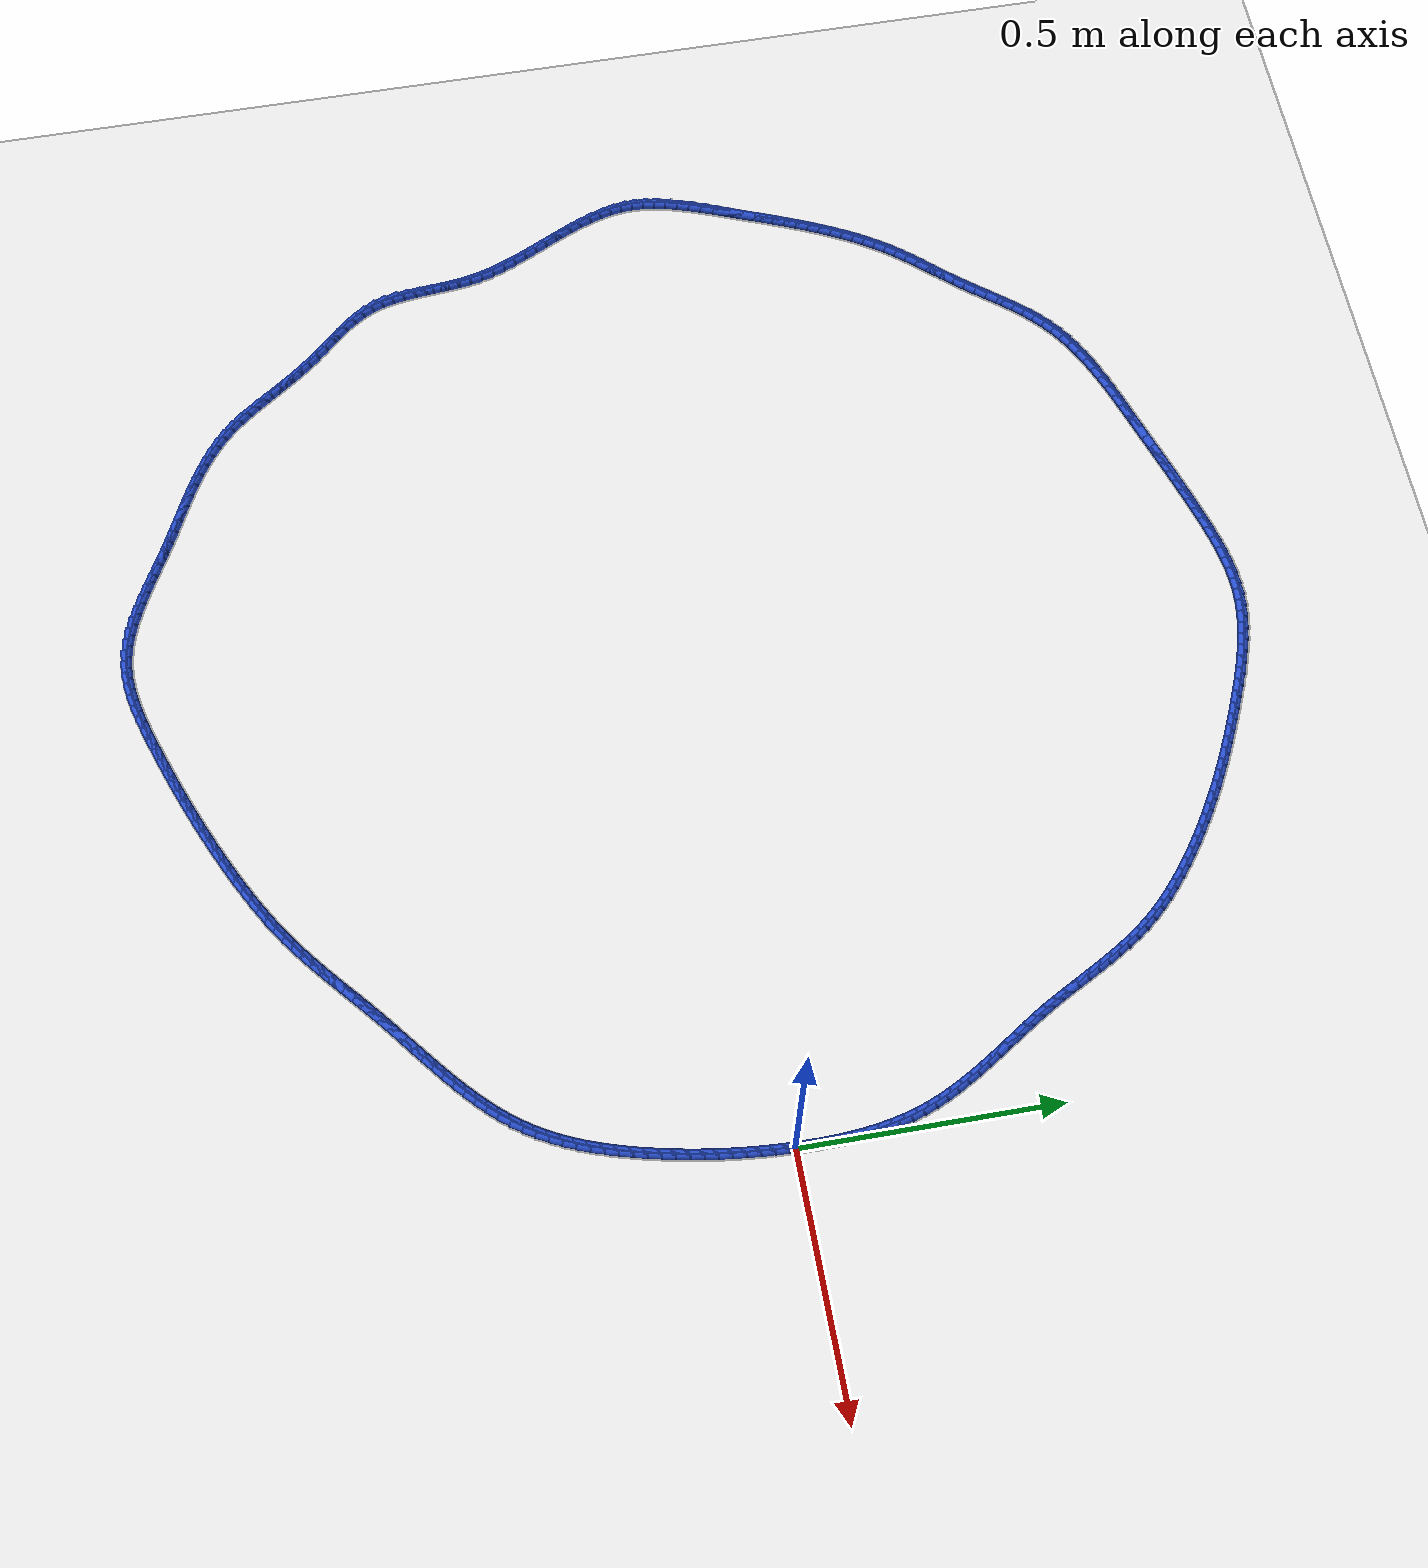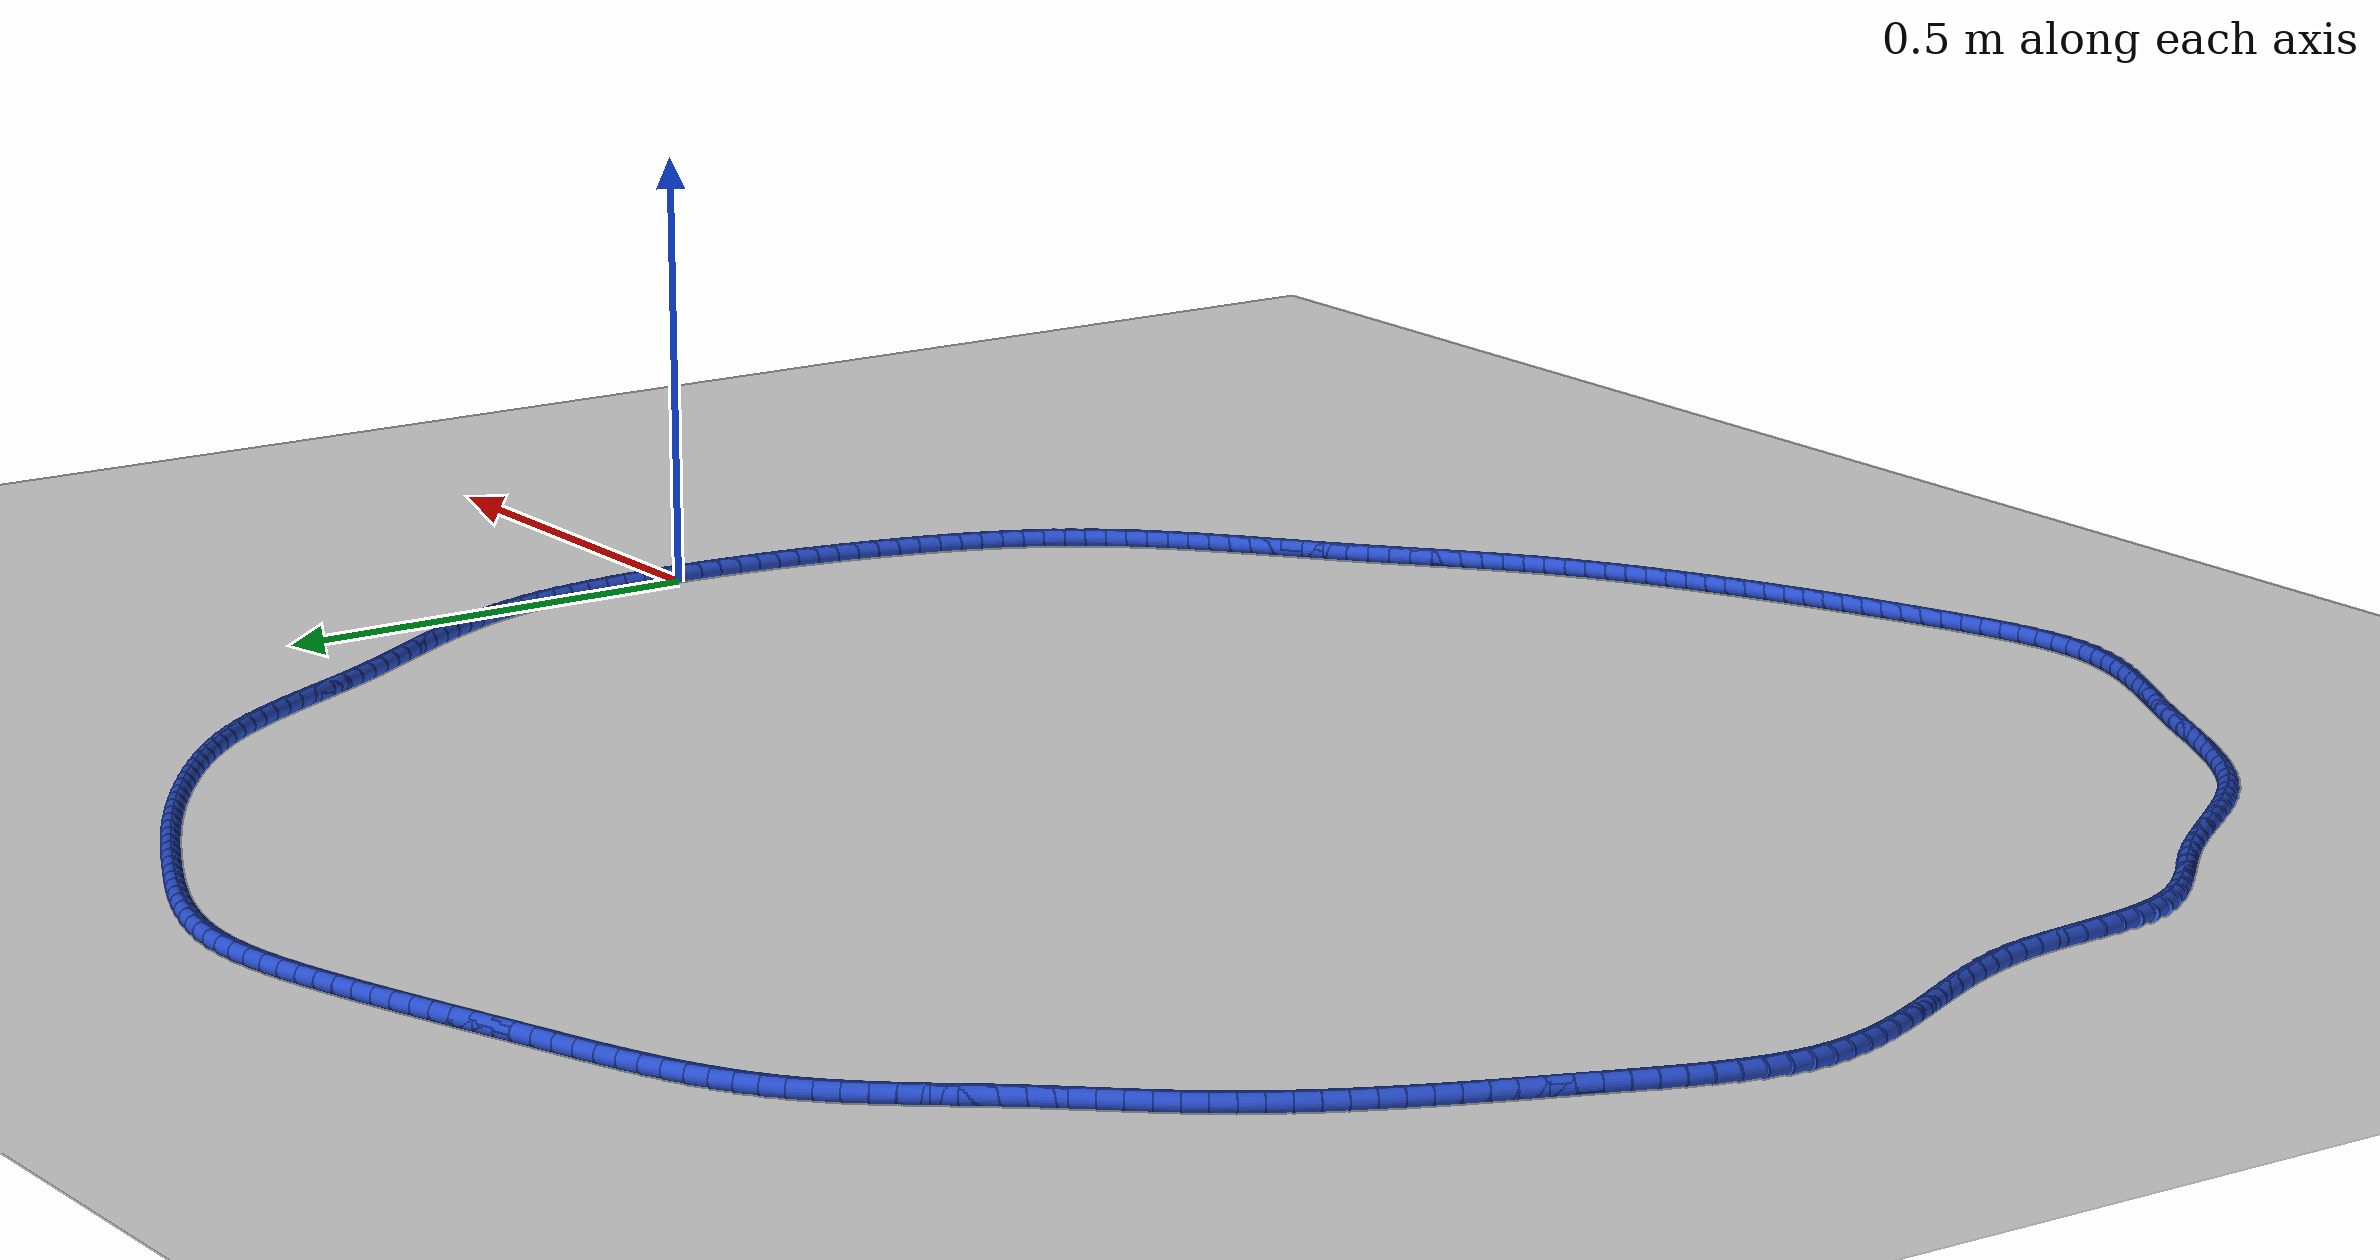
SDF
<sdf version="1.6">
 <world name="default">
  <light name="sun" type="directional">
   <pose>0 0 10 0 -0 0</pose>
   <diffuse>0.8 0.8 0.8 1</diffuse>
   <specular>0.2 0.2 0.2 1</specular>
   <attenuation>
    <range>1000</range>
    <constant>0.9</constant>
    <linear>0.01</linear>
    <quadratic>0.001</quadratic>
   </attenuation>
   <direction>-0.5 0.1 -0.9</direction>
  </light>
  <model name="ground_plane">
   <static>1</static>
   <link name="link">
    <collision name="collision">
     <geometry><plane><normal>0 0 1</normal><size>100 100</size></plane></geometry>
     <surface><friction><ode><mu>100</mu><mu2>50</mu2></ode></friction></surface>
    </collision>
    <visual name="visual">
     <cast_shadows>0</cast_shadows>
     <geometry><plane><normal>0 0 1</normal><size>100 100</size></plane></geometry>
     <material>
      <script><uri>file://media/materials/scripts/gazebo.material</uri><name>Gazebo/WhiteGlow</name></script>
     </material>
    </visual>
   </link>
  </model>
  <gravity>0 0 -9.8</gravity>
  <magnetic_field>6e-06 2.3e-05 -4.2e-05</magnetic_field>
  <atmosphere type="adiabatic"/>
  <physics name="default_physics" default="0" type="ode">
   <max_step_size>0.001</max_step_size>
   <real_time_factor>1</real_time_factor>
   <real_time_update_rate>1000</real_time_update_rate>
  </physics>
  <scene><ambient>0.4 0.4 0.4 1</ambient><background>0.7 0.7 0.7 1</background><shadows>1</shadows></scene>
  <spherical_coordinates>
   <surface_model>EARTH_WGS84</surface_model>
   <latitude_deg>0</latitude_deg>
   <longitude_deg>0</longitude_deg>
   <elevation>0</elevation>
   <heading_deg>0</heading_deg>
  </spherical_coordinates>
  <model name="line">
   <link name="link_0">
    <pose>1.0842021724855044e-17 -2.7755575615628914e-17 0.01 0 1.57 1.5546364044875272</pose>
    <collision name="collision">
     <geometry><cylinder><radius>0.01</radius><length>0.08</length></cylinder></geometry>
    </collision>
    <visual name="visual">
     <material>
      <script><name>Gazebo/Blue</name><uri>file://media/materials/scripts/gazebo.material</uri></script>
     </material>
     <geometry><cylinder><radius>0.01</radius><length>0.08</length></cylinder></geometry>
    </visual>
   </link>
   <link name="link_1">
    <pose>0.0004118270198825984 0.025482249408916132 0.01 0 1.57 -1.564186398989211</pose>
    <collision name="collision">
     <geometry><cylinder><radius>0.01</radius><length>0.08</length></cylinder></geometry>
    </collision>
    <visual name="visual">
     <material>
      <script><name>Gazebo/Blue</name><uri>file://media/materials/scripts/gazebo.material</uri></script>
     </material>
     <geometry><cylinder><radius>0.01</radius><length>0.08</length></cylinder></geometry>
    </visual>
   </link>
   <link name="link_2">
    <pose>0.0002429209052618664 0.05103527505130427 0.01 0 1.57 -1.537986692656326</pose>
    <collision name="collision">
     <geometry><cylinder><radius>0.01</radius><length>0.08</length></cylinder></geometry>
    </collision>
    <visual name="visual">
     <material>
      <script><name>Gazebo/Blue</name><uri>file://media/materials/scripts/gazebo.material</uri></script>
     </material>
     <geometry><cylinder><radius>0.01</radius><length>0.08</length></cylinder></geometry>
    </visual>
   </link>
   <link name="link_3">
    <pose>-0.0005957502410896391 0.07658783640723593 0.01 0 1.57 -1.5081853976924107</pose>
    <collision name="collision">
     <geometry><cylinder><radius>0.01</radius><length>0.08</length></cylinder></geometry>
    </collision>
    <visual name="visual">
     <material>
      <script><name>Gazebo/Blue</name><uri>file://media/materials/scripts/gazebo.material</uri></script>
     </material>
     <geometry><cylinder><radius>0.01</radius><length>0.08</length></cylinder></geometry>
    </visual>
   </link>
   <link name="link_4">
    <pose>-0.002193218316399366 0.10206869295678264 0.01 0 1.57 -1.4745868386641132</pose>
    <collision name="collision">
     <geometry><cylinder><radius>0.01</radius><length>0.08</length></cylinder></geometry>
    </collision>
    <visual name="visual">
     <material>
      <script><name>Gazebo/Blue</name><uri>file://media/materials/scripts/gazebo.material</uri></script>
     </material>
     <geometry><cylinder><radius>0.01</radius><length>0.08</length></cylinder></geometry>
    </visual>
   </link>
   <link name="link_5">
    <pose>-0.0046385152178947675 0.12740660418001598 0.01 0 1.57 -1.4369807490528712</pose>
    <collision name="collision">
     <geometry><cylinder><radius>0.01</radius><length>0.08</length></cylinder></geometry>
    </collision>
    <visual name="visual">
     <material>
      <script><name>Gazebo/Blue</name><uri>file://media/materials/scripts/gazebo.material</uri></script>
     </material>
     <geometry><cylinder><radius>0.01</radius><length>0.08</length></cylinder></geometry>
    </visual>
   </link>
   <link name="link_6">
    <pose>-0.008020672842803292 0.15253032955700746 0.01 0 1.57 -1.3951551702502742</pose>
    <collision name="collision">
     <geometry><cylinder><radius>0.01</radius><length>0.08</length></cylinder></geometry>
    </collision>
    <visual name="visual">
     <material>
      <script><name>Gazebo/Blue</name><uri>file://media/materials/scripts/gazebo.material</uri></script>
     </material>
     <geometry><cylinder><radius>0.01</radius><length>0.08</length></cylinder></geometry>
    </visual>
   </link>
   <link name="link_7">
    <pose>-0.01242872308835239 0.1773686285678287 0.01 0 1.57 -1.3489140348666269</pose>
    <collision name="collision">
     <geometry><cylinder><radius>0.01</radius><length>0.08</length></cylinder></geometry>
    </collision>
    <visual name="visual">
     <material>
      <script><name>Gazebo/Blue</name><uri>file://media/materials/scripts/gazebo.material</uri></script>
     </material>
     <geometry><cylinder><radius>0.01</radius><length>0.08</length></cylinder></geometry>
    </visual>
   </link>
   <link name="link_8">
    <pose>-0.017951697851769515 0.20185026069255116 0.01 0 1.57 -1.298100368414203</pose>
    <collision name="collision">
     <geometry><cylinder><radius>0.01</radius><length>0.08</length></cylinder></geometry>
    </collision>
    <visual name="visual">
     <material>
      <script><name>Gazebo/Blue</name><uri>file://media/materials/scripts/gazebo.material</uri></script>
     </material>
     <geometry><cylinder><radius>0.01</radius><length>0.08</length></cylinder></geometry>
    </visual>
   </link>
   <link name="link_9">
    <pose>-0.024678629030282114 0.2259039854112465 0.01 0 1.57 -1.2427754918187959</pose>
    <collision name="collision">
     <geometry><cylinder><radius>0.01</radius><length>0.08</length></cylinder></geometry>
    </collision>
    <visual name="visual">
     <material>
      <script><name>Gazebo/Blue</name><uri>file://media/materials/scripts/gazebo.material</uri></script>
     </material>
     <geometry><cylinder><radius>0.01</radius><length>0.08</length></cylinder></geometry>
    </visual>
   </link>
   <link name="link_10">
    <pose>-0.03269524403912652 0.24946044079216761 0.01 0 1.57 -1.1878391623554423</pose>
    <collision name="collision">
     <geometry><cylinder><radius>0.01</radius><length>0.08</length></cylinder></geometry>
    </collision>
    <visual name="visual">
     <material>
      <script><name>Gazebo/Blue</name><uri>file://media/materials/scripts/gazebo.material</uri></script>
     </material>
     <geometry><cylinder><radius>0.01</radius><length>0.08</length></cylinder></geometry>
    </visual>
   </link>
   <link name="link_11">
    <pose>-0.04198094604288235 0.27251070992375953 0.01 0 1.57 -1.1393507900521251</pose>
    <collision name="collision">
     <geometry><cylinder><radius>0.01</radius><length>0.08</length></cylinder></geometry>
    </collision>
    <visual name="visual">
     <material>
      <script><name>Gazebo/Blue</name><uri>file://media/materials/scripts/gazebo.material</uri></script>
     </material>
     <geometry><cylinder><radius>0.01</radius><length>0.08</length></cylinder></geometry>
    </visual>
   </link>
   <link name="link_12">
    <pose>-0.05238861409729365 0.2951178044739416 0.01 0 1.57 -1.0978517748861456</pose>
    <collision name="collision">
     <geometry><cylinder><radius>0.01</radius><length>0.08</length></cylinder></geometry>
    </collision>
    <visual name="visual">
     <material>
      <script><name>Gazebo/Blue</name><uri>file://media/materials/scripts/gazebo.material</uri></script>
     </material>
     <geometry><cylinder><radius>0.01</radius><length>0.08</length></cylinder></geometry>
    </visual>
   </link>
   <link name="link_13">
    <pose>-0.06376374444975706 0.31734893321521485 0.01 0 1.57 -1.0633843891883572</pose>
    <collision name="collision">
     <geometry><cylinder><radius>0.01</radius><length>0.08</length></cylinder></geometry>
    </collision>
    <visual name="visual">
     <material>
      <script><name>Gazebo/Blue</name><uri>file://media/materials/scripts/gazebo.material</uri></script>
     </material>
     <geometry><cylinder><radius>0.01</radius><length>0.08</length></cylinder></geometry>
    </visual>
   </link>
   <link name="link_14">
    <pose>-0.07595183334766925 0.3392713049200809 0.01 0 1.57 -1.0358873955832966</pose>
    <collision name="collision">
     <geometry><cylinder><radius>0.01</radius><length>0.08</length></cylinder></geometry>
    </collision>
    <visual name="visual">
     <material>
      <script><name>Gazebo/Blue</name><uri>file://media/materials/scripts/gazebo.material</uri></script>
     </material>
     <geometry><cylinder><radius>0.01</radius><length>0.08</length></cylinder></geometry>
    </visual>
   </link>
   <link name="link_15">
    <pose>-0.08879837703842691 0.360952128361041 0.01 0 1.57 -1.0152474569510226</pose>
    <collision name="collision">
     <geometry><cylinder><radius>0.01</radius><length>0.08</length></cylinder></geometry>
    </collision>
    <visual name="visual">
     <material>
      <script><name>Gazebo/Blue</name><uri>file://media/materials/scripts/gazebo.material</uri></script>
     </material>
     <geometry><cylinder><radius>0.01</radius><length>0.08</length></cylinder></geometry>
    </visual>
   </link>
   <link name="link_16">
    <pose>-0.10214887176942665 0.3824586123105963 0.01 0 1.57 -1.001338742637416</pose>
    <collision name="collision">
     <geometry><cylinder><radius>0.01</radius><length>0.08</length></cylinder></geometry>
    </collision>
    <visual name="visual">
     <material>
      <script><name>Gazebo/Blue</name><uri>file://media/materials/scripts/gazebo.material</uri></script>
     </material>
     <geometry><cylinder><radius>0.01</radius><length>0.08</length></cylinder></geometry>
    </visual>
   </link>
   <link name="link_17">
    <pose>-0.11584881378806516 0.4038579655412483 0.01 0 1.57 -0.9940507604168353</pose>
    <collision name="collision">
     <geometry><cylinder><radius>0.01</radius><length>0.08</length></cylinder></geometry>
    </collision>
    <visual name="visual">
     <material>
      <script><name>Gazebo/Blue</name><uri>file://media/materials/scripts/gazebo.material</uri></script>
     </material>
     <geometry><cylinder><radius>0.01</radius><length>0.08</length></cylinder></geometry>
    </visual>
   </link>
   <link name="link_18">
    <pose>-0.1297436993417391 0.4252173968254984 0.01 0 1.57 -0.993305687983996</pose>
    <collision name="collision">
     <geometry><cylinder><radius>0.01</radius><length>0.08</length></cylinder></geometry>
    </collision>
    <visual name="visual">
     <material>
      <script><name>Gazebo/Blue</name><uri>file://media/materials/scripts/gazebo.material</uri></script>
     </material>
     <geometry><cylinder><radius>0.01</radius><length>0.08</length></cylinder></geometry>
    </visual>
   </link>
   <link name="link_19">
    <pose>-0.14367902467784516 0.44660411493584784 0.01 0 1.57 -0.9990666460265294</pose>
    <collision name="collision">
     <geometry><cylinder><radius>0.01</radius><length>0.08</length></cylinder></geometry>
    </collision>
    <visual name="visual">
     <material>
      <script><name>Gazebo/Blue</name><uri>file://media/materials/scripts/gazebo.material</uri></script>
     </material>
     <geometry><cylinder><radius>0.01</radius><length>0.08</length></cylinder></geometry>
    </visual>
   </link>
   <link name="link_20">
    <pose>-0.15750028604377994 0.4680853286447979 0.01 0 1.57 -1.0113379295031946</pose>
    <collision name="collision">
     <geometry><cylinder><radius>0.01</radius><length>0.08</length></cylinder></geometry>
    </collision>
    <visual name="visual">
     <material>
      <script><name>Gazebo/Blue</name><uri>file://media/materials/scripts/gazebo.material</uri></script>
     </material>
     <geometry><cylinder><radius>0.01</radius><length>0.08</length></cylinder></geometry>
    </visual>
   </link>
   <link name="link_21">
    <pose>-0.17105297968694014 0.4897282467248498 0.01 0 1.57 -1.0301408604105808</pose>
    <collision name="collision">
     <geometry><cylinder><radius>0.01</radius><length>0.08</length></cylinder></geometry>
    </collision>
    <visual name="visual">
     <material>
      <script><name>Gazebo/Blue</name><uri>file://media/materials/scripts/gazebo.material</uri></script>
     </material>
     <geometry><cylinder><radius>0.01</radius><length>0.08</length></cylinder></geometry>
    </visual>
   </link>
   <link name="link_22">
    <pose>-0.18418297655677654 0.511599875001483 0.01 0 1.57 -1.0516298607563073</pose>
    <collision name="collision">
     <geometry><cylinder><radius>0.01</radius><length>0.08</length></cylinder></geometry>
    </collision>
    <visual name="visual">
     <material>
      <script><name>Gazebo/Blue</name><uri>file://media/materials/scripts/gazebo.material</uri></script>
     </material>
     <geometry><cylinder><radius>0.01</radius><length>0.08</length></cylinder></geometry>
    </visual>
   </link>
   <link name="link_23">
    <pose>-0.19682357040221524 0.5337198691546003 0.01 0 1.57 -1.0669363779652152</pose>
    <collision name="collision">
     <geometry><cylinder><radius>0.01</radius><length>0.08</length></cylinder></geometry>
    </collision>
    <visual name="visual">
     <material>
      <script><name>Gazebo/Blue</name><uri>file://media/materials/scripts/gazebo.material</uri></script>
     </material>
     <geometry><cylinder><radius>0.01</radius><length>0.08</length></cylinder></geometry>
    </visual>
   </link>
   <link name="link_24">
    <pose>-0.20910718261338754 0.5560000328751956 0.01 0 1.57 -1.074812422934014</pose>
    <collision name="collision">
     <geometry><cylinder><radius>0.01</radius><length>0.08</length></cylinder></geometry>
    </collision>
    <visual name="visual">
     <material>
      <script><name>Gazebo/Blue</name><uri>file://media/materials/scripts/gazebo.material</uri></script>
     </material>
     <geometry><cylinder><radius>0.01</radius><length>0.08</length></cylinder></geometry>
    </visual>
   </link>
   <link name="link_25">
    <pose>-0.22119382106760366 0.5783372283951507 0.01 0 1.57 -1.0752295521809394</pose>
    <collision name="collision">
     <geometry><cylinder><radius>0.01</radius><length>0.08</length></cylinder></geometry>
    </collision>
    <visual name="visual">
     <material>
      <script><name>Gazebo/Blue</name><uri>file://media/materials/scripts/gazebo.material</uri></script>
     </material>
     <geometry><cylinder><radius>0.01</radius><length>0.08</length></cylinder></geometry>
    </visual>
   </link>
   <link name="link_26">
    <pose>-0.23324349364217345 0.6006283179463463 0.01 0 1.57 -1.068136930244644</pose>
    <collision name="collision">
     <geometry><cylinder><radius>0.01</radius><length>0.08</length></cylinder></geometry>
    </collision>
    <visual name="visual">
     <material>
      <script><name>Gazebo/Blue</name><uri>file://media/materials/scripts/gazebo.material</uri></script>
     </material>
     <geometry><cylinder><radius>0.01</radius><length>0.08</length></cylinder></geometry>
    </visual>
   </link>
   <link name="link_27">
    <pose>-0.2454162082144074 0.6227701637606649 0.01 0 1.57 -1.0534601458558899</pose>
    <collision name="collision">
     <geometry><cylinder><radius>0.01</radius><length>0.08</length></cylinder></geometry>
    </collision>
    <visual name="visual">
     <material>
      <script><name>Gazebo/Blue</name><uri>file://media/materials/scripts/gazebo.material</uri></script>
     </material>
     <geometry><cylinder><radius>0.01</radius><length>0.08</length></cylinder></geometry>
    </visual>
   </link>
   <link name="link_28">
    <pose>-0.2578719726616154 0.6446596280699872 0.01 0 1.57 -1.031112816785467</pose>
    <collision name="collision">
     <geometry><cylinder><radius>0.01</radius><length>0.08</length></cylinder></geometry>
    </collision>
    <visual name="visual">
     <material>
      <script><name>Gazebo/Blue</name><uri>file://media/materials/scripts/gazebo.material</uri></script>
     </material>
     <geometry><cylinder><radius>0.01</radius><length>0.08</length></cylinder></geometry>
    </visual>
   </link>
   <link name="link_29">
    <pose>-0.27077079486110756 0.6661935731061951 0.01 0 1.57 -1.0010219941371528</pose>
    <collision name="collision">
     <geometry><cylinder><radius>0.01</radius><length>0.08</length></cylinder></geometry>
    </collision>
    <visual name="visual">
     <material>
      <script><name>Gazebo/Blue</name><uri>file://media/materials/scripts/gazebo.material</uri></script>
     </material>
     <geometry><cylinder><radius>0.01</radius><length>0.08</length></cylinder></geometry>
    </visual>
   </link>
   <link name="link_30">
    <pose>-0.28427268269019407 0.6872688611011699 0.01 0 1.57 -0.9631682900964806</pose>
    <collision name="collision">
     <geometry><cylinder><radius>0.01</radius><length>0.08</length></cylinder></geometry>
    </collision>
    <visual name="visual">
     <material>
      <script><name>Gazebo/Blue</name><uri>file://media/materials/scripts/gazebo.material</uri></script>
     </material>
     <geometry><cylinder><radius>0.01</radius><length>0.08</length></cylinder></geometry>
    </visual>
   </link>
   <link name="link_31">
    <pose>-0.2985376440261851 0.7077823542867933 0.01 0 1.57 -0.9176427038989327</pose>
    <collision name="collision">
     <geometry><cylinder><radius>0.01</radius><length>0.08</length></cylinder></geometry>
    </collision>
    <visual name="visual">
     <material>
      <script><name>Gazebo/Blue</name><uri>file://media/materials/scripts/gazebo.material</uri></script>
     </material>
     <geometry><cylinder><radius>0.01</radius><length>0.08</length></cylinder></geometry>
    </visual>
   </link>
   <link name="link_32">
    <pose>-0.31372563430440203 0.7276309415227202 0.01 0 1.57 -0.867327904182293</pose>
    <collision name="collision">
     <geometry><cylinder><radius>0.01</radius><length>0.08</length></cylinder></geometry>
    </collision>
    <visual name="visual">
     <material>
      <script><name>Gazebo/Blue</name><uri>file://media/materials/scripts/gazebo.material</uri></script>
     </material>
     <geometry><cylinder><radius>0.01</radius><length>0.08</length></cylinder></geometry>
    </visual>
   </link>
   <link name="link_33">
    <pose>-0.3299363797784009 0.7467420934426271 0.01 0 1.57 -0.8200851813880615</pose>
    <collision name="collision">
     <geometry><cylinder><radius>0.01</radius><length>0.08</length></cylinder></geometry>
    </collision>
    <visual name="visual">
     <material>
      <script><name>Gazebo/Blue</name><uri>file://media/materials/scripts/gazebo.material</uri></script>
     </material>
     <geometry><cylinder><radius>0.01</radius><length>0.08</length></cylinder></geometry>
    </visual>
   </link>
   <link name="link_34">
    <pose>-0.34709346522711926 0.7651327177041435 0.01 0 1.57 -0.777226708189899</pose>
    <collision name="collision">
     <geometry><cylinder><radius>0.01</radius><length>0.08</length></cylinder></geometry>
    </collision>
    <visual name="visual">
     <material>
      <script><name>Gazebo/Blue</name><uri>file://media/materials/scripts/gazebo.material</uri></script>
     </material>
     <geometry><cylinder><radius>0.01</radius><length>0.08</length></cylinder></geometry>
    </visual>
   </link>
   <link name="link_35">
    <pose>-0.3650884458510881 0.7828359851997637 0.01 0 1.57 -0.7386002381840766</pose>
    <collision name="collision">
     <geometry><cylinder><radius>0.01</radius><length>0.08</length></cylinder></geometry>
    </collision>
    <visual name="visual">
     <material>
      <script><name>Gazebo/Blue</name><uri>file://media/materials/scripts/gazebo.material</uri></script>
     </material>
     <geometry><cylinder><radius>0.01</radius><length>0.08</length></cylinder></geometry>
    </visual>
   </link>
   <link name="link_36">
    <pose>-0.3838128768508385 0.7998850668219831 0.01 0 1.57 -0.7040270940454462</pose>
    <collision name="collision">
     <geometry><cylinder><radius>0.01</radius><length>0.08</length></cylinder></geometry>
    </collision>
    <visual name="visual">
     <material>
      <script><name>Gazebo/Blue</name><uri>file://media/materials/scripts/gazebo.material</uri></script>
     </material>
     <geometry><cylinder><radius>0.01</radius><length>0.08</length></cylinder></geometry>
    </visual>
   </link>
   <link name="link_37">
    <pose>-0.4031583134269016 0.8163131334632964 0.01 0 1.57 -0.6733214817426183</pose>
    <collision name="collision">
     <geometry><cylinder><radius>0.01</radius><length>0.08</length></cylinder></geometry>
    </collision>
    <visual name="visual">
     <material>
      <script><name>Gazebo/Blue</name><uri>file://media/materials/scripts/gazebo.material</uri></script>
     </material>
     <geometry><cylinder><radius>0.01</radius><length>0.08</length></cylinder></geometry>
    </visual>
   </link>
   <link name="link_38">
    <pose>-0.42301631077980895 0.8321533560161984 0.01 0 1.57 -0.6463052238405218</pose>
    <collision name="collision">
     <geometry><cylinder><radius>0.01</radius><length>0.08</length></cylinder></geometry>
    </collision>
    <visual name="visual">
     <material>
      <script><name>Gazebo/Blue</name><uri>file://media/materials/scripts/gazebo.material</uri></script>
     </material>
     <geometry><cylinder><radius>0.01</radius><length>0.08</length></cylinder></geometry>
    </visual>
   </link>
   <link name="link_39">
    <pose>-0.4432784241100913 0.8474389053731839 0.01 0 1.57 -0.622744687126072</pose>
    <collision name="collision">
     <geometry><cylinder><radius>0.01</radius><length>0.08</length></cylinder></geometry>
    </collision>
    <visual name="visual">
     <material>
      <script><name>Gazebo/Blue</name><uri>file://media/materials/scripts/gazebo.material</uri></script>
     </material>
     <geometry><cylinder><radius>0.01</radius><length>0.08</length></cylinder></geometry>
    </visual>
   </link>
   <link name="link_40">
    <pose>-0.46383908519687694 0.8622027083370429 0.01 0 1.57 -0.6011629150890239</pose>
    <collision name="collision">
     <geometry><cylinder><radius>0.01</radius><length>0.08</length></cylinder></geometry>
    </collision>
    <visual name="visual">
     <material>
      <script><name>Gazebo/Blue</name><uri>file://media/materials/scripts/gazebo.material</uri></script>
     </material>
     <geometry><cylinder><radius>0.01</radius><length>0.08</length></cylinder></geometry>
    </visual>
   </link>
   <link name="link_41">
    <pose>-0.48464617709727753 0.8764731561464427 0.01 0 1.57 -0.5803682896140858</pose>
    <collision name="collision">
     <geometry><cylinder><radius>0.01</radius><length>0.08</length></cylinder></geometry>
    </collision>
    <visual name="visual">
     <material>
      <script><name>Gazebo/Blue</name><uri>file://media/materials/scripts/gazebo.material</uri></script>
     </material>
     <geometry><cylinder><radius>0.01</radius><length>0.08</length></cylinder></geometry>
    </visual>
   </link>
   <link name="link_42">
    <pose>-0.5056948020732575 0.8902746332933572 0.01 0 1.57 -0.5603692012227842</pose>
    <collision name="collision">
     <geometry><cylinder><radius>0.01</radius><length>0.08</length></cylinder></geometry>
    </collision>
    <visual name="visual">
     <material>
      <script><name>Gazebo/Blue</name><uri>file://media/materials/scripts/gazebo.material</uri></script>
     </material>
     <geometry><cylinder><radius>0.01</radius><length>0.08</length></cylinder></geometry>
    </visual>
   </link>
   <link name="link_43">
    <pose>-0.5269816865428136 0.9036313864533383 0.01 0 1.57 -0.5412101676311466</pose>
    <collision name="collision">
     <geometry><cylinder><radius>0.01</radius><length>0.08</length></cylinder></geometry>
    </collision>
    <visual name="visual">
     <material>
      <script><name>Gazebo/Blue</name><uri>file://media/materials/scripts/gazebo.material</uri></script>
     </material>
     <geometry><cylinder><radius>0.01</radius><length>0.08</length></cylinder></geometry>
    </visual>
   </link>
   <link name="link_44">
    <pose>-0.5485035569239433 0.916567662301938 0.01 0 1.57 -0.5229299510721955</pose>
    <collision name="collision">
     <geometry><cylinder><radius>0.01</radius><length>0.08</length></cylinder></geometry>
    </collision>
    <visual name="visual">
     <material>
      <script><name>Gazebo/Blue</name><uri>file://media/materials/scripts/gazebo.material</uri></script>
     </material>
     <geometry><cylinder><radius>0.01</radius><length>0.08</length></cylinder></geometry>
    </visual>
   </link>
   <link name="link_45">
    <pose>-0.5702571396346438 0.9291077075147088 0.01 0 1.57 -0.5055616325346642</pose>
    <collision name="collision">
     <geometry><cylinder><radius>0.01</radius><length>0.08</length></cylinder></geometry>
    </collision>
    <visual name="visual">
     <material>
      <script><name>Gazebo/Blue</name><uri>file://media/materials/scripts/gazebo.material</uri></script>
     </material>
     <geometry><cylinder><radius>0.01</radius><length>0.08</length></cylinder></geometry>
    </visual>
   </link>
   <link name="link_46">
    <pose>-0.5922391610929125 0.9412757687672028 0.01 0 1.57 -0.4891327814604529</pose>
    <collision name="collision">
     <geometry><cylinder><radius>0.01</radius><length>0.08</length></cylinder></geometry>
    </collision>
    <visual name="visual">
     <material>
      <script><name>Gazebo/Blue</name><uri>file://media/materials/scripts/gazebo.material</uri></script>
     </material>
     <geometry><cylinder><radius>0.01</radius><length>0.08</length></cylinder></geometry>
    </visual>
   </link>
   <link name="link_47">
    <pose>-0.6144463477167464 0.9530960927349719 0.01 0 1.57 -0.4736657036567464</pose>
    <collision name="collision">
     <geometry><cylinder><radius>0.01</radius><length>0.08</length></cylinder></geometry>
    </collision>
    <visual name="visual">
     <material>
      <script><name>Gazebo/Blue</name><uri>file://media/materials/scripts/gazebo.material</uri></script>
     </material>
     <geometry><cylinder><radius>0.01</radius><length>0.08</length></cylinder></geometry>
    </visual>
   </link>
   <link name="link_48">
    <pose>-0.6368754259241426 0.9645929260935681 0.01 0 1.57 -0.4591777497540767</pose>
    <collision name="collision">
     <geometry><cylinder><radius>0.01</radius><length>0.08</length></cylinder></geometry>
    </collision>
    <visual name="visual">
     <material>
      <script><name>Gazebo/Blue</name><uri>file://media/materials/scripts/gazebo.material</uri></script>
     </material>
     <geometry><cylinder><radius>0.01</radius><length>0.08</length></cylinder></geometry>
    </visual>
   </link>
   <link name="link_49">
    <pose>-0.6595231221330988 0.9757905155185445 0.01 0 1.57 -0.44568166702992895</pose>
    <collision name="collision">
     <geometry><cylinder><radius>0.01</radius><length>0.08</length></cylinder></geometry>
    </collision>
    <visual name="visual">
     <material>
      <script><name>Gazebo/Blue</name><uri>file://media/materials/scripts/gazebo.material</uri></script>
     </material>
     <geometry><cylinder><radius>0.01</radius><length>0.08</length></cylinder></geometry>
    </visual>
   </link>
   <link name="link_50">
    <pose>-0.6823861627616121 0.9867131076854524 0.01 0 1.57 -0.43318597861476743</pose>
    <collision name="collision">
     <geometry><cylinder><radius>0.01</radius><length>0.08</length></cylinder></geometry>
    </collision>
    <visual name="visual">
     <material>
      <script><name>Gazebo/Blue</name><uri>file://media/materials/scripts/gazebo.material</uri></script>
     </material>
     <geometry><cylinder><radius>0.01</radius><length>0.08</length></cylinder></geometry>
    </visual>
   </link>
   <link name="link_51">
    <pose>-0.7054612742276793 0.9973849492698441 0.01 0 1.57 -0.4216953757877235</pose>
    <collision name="collision">
     <geometry><cylinder><radius>0.01</radius><length>0.08</length></cylinder></geometry>
    </collision>
    <visual name="visual">
     <material>
      <script><name>Gazebo/Blue</name><uri>file://media/materials/scripts/gazebo.material</uri></script>
     </material>
     <geometry><cylinder><radius>0.01</radius><length>0.08</length></cylinder></geometry>
    </visual>
   </link>
   <link name="link_52">
    <pose>-0.728745182949298 1.007830286947272 0.01 0 1.57 -0.41104274833403714</pose>
    <collision name="collision">
     <geometry><cylinder><radius>0.01</radius><length>0.08</length></cylinder></geometry>
    </collision>
    <visual name="visual">
     <material>
      <script><name>Gazebo/Blue</name><uri>file://media/materials/scripts/gazebo.material</uri></script>
     </material>
     <geometry><cylinder><radius>0.01</radius><length>0.08</length></cylinder></geometry>
    </visual>
   </link>
   <link name="link_53">
    <pose>-0.7522343967160035 1.018068565671057 0.01 0 1.57 -0.3978588674061662</pose>
    <collision name="collision">
     <geometry><cylinder><radius>0.01</radius><length>0.08</length></cylinder></geometry>
    </collision>
    <visual name="visual">
     <material>
      <script><name>Gazebo/Blue</name><uri>file://media/materials/scripts/gazebo.material</uri></script>
     </material>
     <geometry><cylinder><radius>0.01</radius><length>0.08</length></cylinder></geometry>
    </visual>
   </link>
   <link name="link_54">
    <pose>-0.7759210599572829 1.028023398210745 0.01 0 1.57 -0.3789796508628956</pose>
    <collision name="collision">
     <geometry><cylinder><radius>0.01</radius><length>0.08</length></cylinder></geometry>
    </collision>
    <visual name="visual">
     <material>
      <script><name>Gazebo/Blue</name><uri>file://media/materials/scripts/gazebo.material</uri></script>
     </material>
     <geometry><cylinder><radius>0.01</radius><length>0.08</length></cylinder></geometry>
    </visual>
   </link>
   <link name="link_55">
    <pose>-0.7997932940746526 1.0375300398426746 0.01 0 1.57 -0.3541408575236066</pose>
    <collision name="collision">
     <geometry><cylinder><radius>0.01</radius><length>0.08</length></cylinder></geometry>
    </collision>
    <visual name="visual">
     <material>
      <script><name>Gazebo/Blue</name><uri>file://media/materials/scripts/gazebo.material</uri></script>
     </material>
     <geometry><cylinder><radius>0.01</radius><length>0.08</length></cylinder></geometry>
    </visual>
   </link>
   <link name="link_56">
    <pose>-0.8238390700483269 1.0464204421502306 0.01 0 1.57 -0.3231262213969185</pose>
    <collision name="collision">
     <geometry><cylinder><radius>0.01</radius><length>0.08</length></cylinder></geometry>
    </collision>
    <visual name="visual">
     <material>
      <script><name>Gazebo/Blue</name><uri>file://media/materials/scripts/gazebo.material</uri></script>
     </material>
     <geometry><cylinder><radius>0.01</radius><length>0.08</length></cylinder></geometry>
    </visual>
   </link>
   <link name="link_57">
    <pose>-0.8480463588585204 1.0545265567167992 0.01 0 1.57 -0.28567434669091757</pose>
    <collision name="collision">
     <geometry><cylinder><radius>0.01</radius><length>0.08</length></cylinder></geometry>
    </collision>
    <visual name="visual">
     <material>
      <script><name>Gazebo/Blue</name><uri>file://media/materials/scripts/gazebo.material</uri></script>
     </material>
     <geometry><cylinder><radius>0.01</radius><length>0.08</length></cylinder></geometry>
    </visual>
   </link>
   <link name="link_58">
    <pose>-0.8724031314854485 1.0616803351257653 0.01 0 1.57 -0.2415112120452074</pose>
    <collision name="collision">
     <geometry><cylinder><radius>0.01</radius><length>0.08</length></cylinder></geometry>
    </collision>
    <visual name="visual">
     <material>
      <script><name>Gazebo/Blue</name><uri>file://media/materials/scripts/gazebo.material</uri></script>
     </material>
     <geometry><cylinder><radius>0.01</radius><length>0.08</length></cylinder></geometry>
    </visual>
   </link>
   <link name="link_59">
    <pose>-0.8968973589093244 1.0677137289605143 0.01 0 1.57 -0.19039609347358924</pose>
    <collision name="collision">
     <geometry><cylinder><radius>0.01</radius><length>0.08</length></cylinder></geometry>
    </collision>
    <visual name="visual">
     <material>
      <script><name>Gazebo/Blue</name><uri>file://media/materials/scripts/gazebo.material</uri></script>
     </material>
     <geometry><cylinder><radius>0.01</radius><length>0.08</length></cylinder></geometry>
    </visual>
   </link>
   <link name="link_60">
    <pose>-0.9215170121103634 1.0724586898044315 0.01 0 1.57 -0.13218363398075433</pose>
    <collision name="collision">
     <geometry><cylinder><radius>0.01</radius><length>0.08</length></cylinder></geometry>
    </collision>
    <visual name="visual">
     <material>
      <script><name>Gazebo/Blue</name><uri>file://media/materials/scripts/gazebo.material</uri></script>
     </material>
     <geometry><cylinder><radius>0.01</radius><length>0.08</length></cylinder></geometry>
    </visual>
   </link>
   <link name="link_61">
    <pose>-0.9462500620687799 1.0757471692409024 0.01 0 1.57 -0.06690176368433222</pose>
    <collision name="collision">
     <geometry><cylinder><radius>0.01</radius><length>0.08</length></cylinder></geometry>
    </collision>
    <visual name="visual">
     <material>
      <script><name>Gazebo/Blue</name><uri>file://media/materials/scripts/gazebo.material</uri></script>
     </material>
     <geometry><cylinder><radius>0.01</radius><length>0.08</length></cylinder></geometry>
    </visual>
   </link>
   <link name="link_62">
    <pose>-0.971084479764789 1.0774111188533122 0.01 0 1.57 0.0030754773394463305</pose>
    <collision name="collision">
     <geometry><cylinder><radius>0.01</radius><length>0.08</length></cylinder></geometry>
    </collision>
    <visual name="visual">
     <material>
      <script><name>Gazebo/Blue</name><uri>file://media/materials/scripts/gazebo.material</uri></script>
     </material>
     <geometry><cylinder><radius>0.01</radius><length>0.08</length></cylinder></geometry>
    </visual>
   </link>
   <link name="link_63">
    <pose>-0.9960045848867498 1.0773344773930735 0.01 0 1.57 0.06731471541964741</pose>
    <collision name="collision">
     <geometry><cylinder><radius>0.01</radius><length>0.08</length></cylinder></geometry>
    </collision>
    <visual name="visual">
     <material>
      <script><name>Gazebo/Blue</name><uri>file://media/materials/scripts/gazebo.material</uri></script>
     </material>
     <geometry><cylinder><radius>0.01</radius><length>0.08</length></cylinder></geometry>
    </visual>
   </link>
   <link name="link_64">
    <pose>-1.0209771575715214 1.0756509121041924 0.01 0 1.57 0.12272356616300831</pose>
    <collision name="collision">
     <geometry><cylinder><radius>0.01</radius><length>0.08</length></cylinder></geometry>
    </collision>
    <visual name="visual">
     <material>
      <script><name>Gazebo/Blue</name><uri>file://media/materials/scripts/gazebo.material</uri></script>
     </material>
     <geometry><cylinder><radius>0.01</radius><length>0.08</length></cylinder></geometry>
    </visual>
   </link>
   <link name="link_65">
    <pose>-1.0459637178035281 1.072568984388533 0.01 0 1.57 0.16948650251394934</pose>
    <collision name="collision">
     <geometry><cylinder><radius>0.01</radius><length>0.08</length></cylinder></geometry>
    </collision>
    <visual name="visual">
     <material>
      <script><name>Gazebo/Blue</name><uri>file://media/materials/scripts/gazebo.material</uri></script>
     </material>
     <geometry><cylinder><radius>0.01</radius><length>0.08</length></cylinder></geometry>
    </visual>
   </link>
   <link name="link_66">
    <pose>-1.0709257845715596 1.0682972698237867 0.01 0 1.57 0.207919671183176</pose>
    <collision name="collision">
     <geometry><cylinder><radius>0.01</radius><length>0.08</length></cylinder></geometry>
    </collision>
    <visual name="visual">
     <material>
      <script><name>Gazebo/Blue</name><uri>file://media/materials/scripts/gazebo.material</uri></script>
     </material>
     <geometry><cylinder><radius>0.01</radius><length>0.08</length></cylinder></geometry>
    </visual>
   </link>
   <link name="link_67">
    <pose>-1.0958248768644085 1.0630443439876456 0.01 0 1.57 0.23836959375116112</pose>
    <collision name="collision">
     <geometry><cylinder><radius>0.01</radius><length>0.08</length></cylinder></geometry>
    </collision>
    <visual name="visual">
     <material>
      <script><name>Gazebo/Blue</name><uri>file://media/materials/scripts/gazebo.material</uri></script>
     </material>
     <geometry><cylinder><radius>0.01</radius><length>0.08</length></cylinder></geometry>
    </visual>
   </link>
   <link name="link_68">
    <pose>-1.1206225136708647 1.0570187824578012 0.01 0 1.57 0.26114128751461496</pose>
    <collision name="collision">
     <geometry><cylinder><radius>0.01</radius><length>0.08</length></cylinder></geometry>
    </collision>
    <visual name="visual">
     <material>
      <script><name>Gazebo/Blue</name><uri>file://media/materials/scripts/gazebo.material</uri></script>
     </material>
     <geometry><cylinder><radius>0.01</radius><length>0.08</length></cylinder></geometry>
    </visual>
   </link>
   <link name="link_69">
    <pose>-1.1452802139797196 1.0504291608119447 0.01 0 1.57 0.2764508847128336</pose>
    <collision name="collision">
     <geometry><cylinder><radius>0.01</radius><length>0.08</length></cylinder></geometry>
    </collision>
    <visual name="visual">
     <material>
      <script><name>Gazebo/Blue</name><uri>file://media/materials/scripts/gazebo.material</uri></script>
     </material>
     <geometry><cylinder><radius>0.01</radius><length>0.08</length></cylinder></geometry>
    </visual>
   </link>
   <link name="link_70">
    <pose>-1.1697595203626392 1.043483998624131 0.01 0 1.57 0.28587610004820185</pose>
    <collision name="collision">
     <geometry><cylinder><radius>0.01</radius><length>0.08</length></cylinder></geometry>
    </collision>
    <visual name="visual">
     <material>
      <script><name>Gazebo/Blue</name><uri>file://media/materials/scripts/gazebo.material</uri></script>
     </material>
     <geometry><cylinder><radius>0.01</radius><length>0.08</length></cylinder></geometry>
    </visual>
   </link>
   <link name="link_71">
    <pose>-1.1940408193171363 1.0363470656909701 0.01 0 1.57 0.2935571192196816</pose>
    <collision name="collision">
     <geometry><cylinder><radius>0.01</radius><length>0.08</length></cylinder></geometry>
    </collision>
    <visual name="visual">
     <material>
      <script><name>Gazebo/Blue</name><uri>file://media/materials/scripts/gazebo.material</uri></script>
     </material>
     <geometry><cylinder><radius>0.01</radius><length>0.08</length></cylinder></geometry>
    </visual>
   </link>
   <link name="link_72">
    <pose>-1.2181572337983408 1.029056895445872 0.01 0 1.57 0.30016967015858065</pose>
    <collision name="collision">
     <geometry><cylinder><radius>0.01</radius><length>0.08</length></cylinder></geometry>
    </collision>
    <visual name="visual">
     <material>
      <script><name>Gazebo/Blue</name><uri>file://media/materials/scripts/gazebo.material</uri></script>
     </material>
     <geometry><cylinder><radius>0.01</radius><length>0.08</length></cylinder></geometry>
    </visual>
   </link>
   <link name="link_73">
    <pose>-1.2421510419305883 1.0216302800042354 0.01 0 1.57 0.3056751671598404</pose>
    <collision name="collision">
     <geometry><cylinder><radius>0.01</radius><length>0.08</length></cylinder></geometry>
    </collision>
    <visual name="visual">
     <material>
      <script><name>Gazebo/Blue</name><uri>file://media/materials/scripts/gazebo.material</uri></script>
     </material>
     <geometry><cylinder><radius>0.01</radius><length>0.08</length></cylinder></geometry>
    </visual>
   </link>
   <link name="link_74">
    <pose>-1.2660645218382154 1.0140840114814602 0.01 0 1.57 0.310044543074216</pose>
    <collision name="collision">
     <geometry><cylinder><radius>0.01</radius><length>0.08</length></cylinder></geometry>
    </collision>
    <visual name="visual">
     <material>
      <script><name>Gazebo/Blue</name><uri>file://media/materials/scripts/gazebo.material</uri></script>
     </material>
     <geometry><cylinder><radius>0.01</radius><length>0.08</length></cylinder></geometry>
    </visual>
   </link>
   <link name="link_75">
    <pose>-1.2899399516455572 1.006434881992945 0.01 0 1.57 0.3132585399794946</pose>
    <collision name="collision">
     <geometry><cylinder><radius>0.01</radius><length>0.08</length></cylinder></geometry>
    </collision>
    <visual name="visual">
     <material>
      <script><name>Gazebo/Blue</name><uri>file://media/materials/scripts/gazebo.material</uri></script>
     </material>
     <geometry><cylinder><radius>0.01</radius><length>0.08</length></cylinder></geometry>
    </visual>
   </link>
   <link name="link_76">
    <pose>-1.3138196094769499 0.9986996836540889 0.01 0 1.57 0.31530782320399275</pose>
    <collision name="collision">
     <geometry><cylinder><radius>0.01</radius><length>0.08</length></cylinder></geometry>
    </collision>
    <visual name="visual">
     <material>
      <script><name>Gazebo/Blue</name><uri>file://media/materials/scripts/gazebo.material</uri></script>
     </material>
     <geometry><cylinder><radius>0.01</radius><length>0.08</length></cylinder></geometry>
    </visual>
   </link>
   <link name="link_77">
    <pose>-1.3377457734567293 0.9908952085802912 0.01 0 1.57 0.31619292521042125</pose>
    <collision name="collision">
     <geometry><cylinder><radius>0.01</radius><length>0.08</length></cylinder></geometry>
    </collision>
    <visual name="visual">
     <material>
      <script><name>Gazebo/Blue</name><uri>file://media/materials/scripts/gazebo.material</uri></script>
     </material>
     <geometry><cylinder><radius>0.01</radius><length>0.08</length></cylinder></geometry>
    </visual>
   </link>
   <link name="link_78">
    <pose>-1.3617607217092318 0.9830382488869508 0.01 0 1.57 0.31592402913411954</pose>
    <collision name="collision">
     <geometry><cylinder><radius>0.01</radius><length>0.08</length></cylinder></geometry>
    </collision>
    <visual name="visual">
     <material>
      <script><name>Gazebo/Blue</name><uri>file://media/materials/scripts/gazebo.material</uri></script>
     </material>
     <geometry><cylinder><radius>0.01</radius><length>0.08</length></cylinder></geometry>
    </visual>
   </link>
   <link name="link_79">
    <pose>-1.3859067323587915 0.9751455966894665 0.01 0 1.57 0.3149775887304113</pose>
    <collision name="collision">
     <geometry><cylinder><radius>0.01</radius><length>0.08</length></cylinder></geometry>
    </collision>
    <visual name="visual">
     <material>
      <script><name>Gazebo/Blue</name><uri>file://media/materials/scripts/gazebo.material</uri></script>
     </material>
     <geometry><cylinder><radius>0.01</radius><length>0.08</length></cylinder></geometry>
    </visual>
   </link>
   <link name="link_80">
    <pose>-1.4102158289366342 0.9672250937292876 0.01 0 1.57 0.31752404117702204</pose>
    <collision name="collision">
     <geometry><cylinder><radius>0.01</radius><length>0.08</length></cylinder></geometry>
    </collision>
    <visual name="visual">
     <material>
      <script><name>Gazebo/Blue</name><uri>file://media/materials/scripts/gazebo.material</uri></script>
     </material>
     <geometry><cylinder><radius>0.01</radius><length>0.08</length></cylinder></geometry>
    </visual>
   </link>
   <link name="link_81">
    <pose>-1.434626279805508 0.9592027507275063 0.01 0 1.57 0.32575678194027496</pose>
    <collision name="collision">
     <geometry><cylinder><radius>0.01</radius><length>0.08</length></cylinder></geometry>
    </collision>
    <visual name="visual">
     <material>
      <script><name>Gazebo/Blue</name><uri>file://media/materials/scripts/gazebo.material</uri></script>
     </material>
     <geometry><cylinder><radius>0.01</radius><length>0.08</length></cylinder></geometry>
    </visual>
   </link>
   <link name="link_82">
    <pose>-1.459026102097768 0.9509607183223612 0.01 0 1.57 0.33972220007475834</pose>
    <collision name="collision">
     <geometry><cylinder><radius>0.01</radius><length>0.08</length></cylinder></geometry>
    </collision>
    <visual name="visual">
     <material>
      <script><name>Gazebo/Blue</name><uri>file://media/materials/scripts/gazebo.material</uri></script>
     </material>
     <geometry><cylinder><radius>0.01</radius><length>0.08</length></cylinder></geometry>
    </visual>
   </link>
   <link name="link_83">
    <pose>-1.483302834867046 0.9423807298772864 0.01 0 1.57 0.3595277951602803</pose>
    <collision name="collision">
     <geometry><cylinder><radius>0.01</radius><length>0.08</length></cylinder></geometry>
    </collision>
    <visual name="visual">
     <material>
      <script><name>Gazebo/Blue</name><uri>file://media/materials/scripts/gazebo.material</uri></script>
     </material>
     <geometry><cylinder><radius>0.01</radius><length>0.08</length></cylinder></geometry>
    </visual>
   </link>
   <link name="link_84">
    <pose>-1.5073440171669759 0.9333445187557163 0.01 0 1.57 0.38535181601708507</pose>
    <collision name="collision">
     <geometry><cylinder><radius>0.01</radius><length>0.08</length></cylinder></geometry>
    </collision>
    <visual name="visual">
     <material>
      <script><name>Gazebo/Blue</name><uri>file://media/materials/scripts/gazebo.material</uri></script>
     </material>
     <geometry><cylinder><radius>0.01</radius><length>0.08</length></cylinder></geometry>
    </visual>
   </link>
   <link name="link_85">
    <pose>-1.5310371880511882 0.9237338183210844 0.01 0 1.57 0.4174265664303013</pose>
    <collision name="collision">
     <geometry><cylinder><radius>0.01</radius><length>0.08</length></cylinder></geometry>
    </collision>
    <visual name="visual">
     <material>
      <script><name>Gazebo/Blue</name><uri>file://media/materials/scripts/gazebo.material</uri></script>
     </material>
     <geometry><cylinder><radius>0.01</radius><length>0.08</length></cylinder></geometry>
    </visual>
   </link>
   <link name="link_86">
    <pose>-1.5542698865733173 0.9134303619368249 0.01 0 1.57 0.4560139336835053</pose>
    <collision name="collision">
     <geometry><cylinder><radius>0.01</radius><length>0.08</length></cylinder></geometry>
    </collision>
    <visual name="visual">
     <material>
      <script><name>Gazebo/Blue</name><uri>file://media/materials/scripts/gazebo.material</uri></script>
     </material>
     <geometry><cylinder><radius>0.01</radius><length>0.08</length></cylinder></geometry>
    </visual>
   </link>
   <link name="link_87">
    <pose>-1.576929651786995 0.9023158829663724 0.01 0 1.57 0.5013698508926541</pose>
    <collision name="collision">
     <geometry><cylinder><radius>0.01</radius><length>0.08</length></cylinder></geometry>
    </collision>
    <visual name="visual">
     <material>
      <script><name>Gazebo/Blue</name><uri>file://media/materials/scripts/gazebo.material</uri></script>
     </material>
     <geometry><cylinder><radius>0.01</radius><length>0.08</length></cylinder></geometry>
    </visual>
   </link>
   <link name="link_88">
    <pose>-1.5989040227458537 0.8902721147731602 0.01 0 1.57 0.5536945455587712</pose>
    <collision name="collision">
     <geometry><cylinder><radius>0.01</radius><length>0.08</length></cylinder></geometry>
    </collision>
    <visual name="visual">
     <material>
      <script><name>Gazebo/Blue</name><uri>file://media/materials/scripts/gazebo.material</uri></script>
     </material>
     <geometry><cylinder><radius>0.01</radius><length>0.08</length></cylinder></geometry>
    </visual>
   </link>
   <link name="link_89">
    <pose>-1.6200805385035268 0.8771807907206227 0.01 0 1.57 0.6130669753876479</pose>
    <collision name="collision">
     <geometry><cylinder><radius>0.01</radius><length>0.08</length></cylinder></geometry>
    </collision>
    <visual name="visual">
     <material>
      <script><name>Gazebo/Blue</name><uri>file://media/materials/scripts/gazebo.material</uri></script>
     </material>
     <geometry><cylinder><radius>0.01</radius><length>0.08</length></cylinder></geometry>
    </visual>
   </link>
   <link name="link_90">
    <pose>-1.640346738113646 0.8629236441721937 0.01 0 1.57 0.6792917852148674</pose>
    <collision name="collision">
     <geometry><cylinder><radius>0.01</radius><length>0.08</length></cylinder></geometry>
    </collision>
    <visual name="visual">
     <material>
      <script><name>Gazebo/Blue</name><uri>file://media/materials/scripts/gazebo.material</uri></script>
     </material>
     <geometry><cylinder><radius>0.01</radius><length>0.08</length></cylinder></geometry>
    </visual>
   </link>
   <link name="link_91">
    <pose>-1.6595913738178072 0.847383779711571 0.01 0 1.57 0.7457448923654022</pose>
    <collision name="collision">
     <geometry><cylinder><radius>0.01</radius><length>0.08</length></cylinder></geometry>
    </collision>
    <visual name="visual">
     <material>
      <script><name>Gazebo/Blue</name><uri>file://media/materials/scripts/gazebo.material</uri></script>
     </material>
     <geometry><cylinder><radius>0.01</radius><length>0.08</length></cylinder></geometry>
    </visual>
   </link>
   <link name="link_92">
    <pose>-1.6778054168298182 0.830559836143301 0.01 0 1.57 0.801148146514581</pose>
    <collision name="collision">
     <geometry><cylinder><radius>0.01</radius><length>0.08</length></cylinder></geometry>
    </collision>
    <visual name="visual">
     <material>
      <script><name>Gazebo/Blue</name><uri>file://media/materials/scripts/gazebo.material</uri></script>
     </material>
     <geometry><cylinder><radius>0.01</radius><length>0.08</length></cylinder></geometry>
    </visual>
   </link>
   <link name="link_93">
    <pose>-1.6951580148613614 0.8126518383983024 0.01 0 1.57 0.8443878576699791</pose>
    <collision name="collision">
     <geometry><cylinder><radius>0.01</radius><length>0.08</length></cylinder></geometry>
    </collision>
    <visual name="visual">
     <material>
      <script><name>Gazebo/Blue</name><uri>file://media/materials/scripts/gazebo.material</uri></script>
     </material>
     <geometry><cylinder><radius>0.01</radius><length>0.08</length></cylinder></geometry>
    </visual>
   </link>
   <link name="link_94">
    <pose>-1.7118362067216666 0.7938800330353404 0.01 0 1.57 0.8757130713860872</pose>
    <collision name="collision">
     <geometry><cylinder><radius>0.01</radius><length>0.08</length></cylinder></geometry>
    </collision>
    <visual name="visual">
     <material>
      <script><name>Gazebo/Blue</name><uri>file://media/materials/scripts/gazebo.material</uri></script>
     </material>
     <geometry><cylinder><radius>0.01</radius><length>0.08</length></cylinder></geometry>
    </visual>
   </link>
   <link name="link_95">
    <pose>-1.7280270312199602 0.7744646666131806 0.01 0 1.57 0.8954547529954168</pose>
    <collision name="collision">
     <geometry><cylinder><radius>0.01</radius><length>0.08</length></cylinder></geometry>
    </collision>
    <visual name="visual">
     <material>
      <script><name>Gazebo/Blue</name><uri>file://media/materials/scripts/gazebo.material</uri></script>
     </material>
     <geometry><cylinder><radius>0.01</radius><length>0.08</length></cylinder></geometry>
    </visual>
   </link>
   <link name="link_96">
    <pose>-1.74391752716547 0.7546259856905876 0.01 0 1.57 0.9038986202210106</pose>
    <collision name="collision">
     <geometry><cylinder><radius>0.01</radius><length>0.08</length></cylinder></geometry>
    </collision>
    <visual name="visual">
     <material>
      <script><name>Gazebo/Blue</name><uri>file://media/materials/scripts/gazebo.material</uri></script>
     </material>
     <geometry><cylinder><radius>0.01</radius><length>0.08</length></cylinder></geometry>
    </visual>
   </link>
   <link name="link_97">
    <pose>-1.759694733367425 0.7345842368263267 0.01 0 1.57 0.901213547198104</pose>
    <collision name="collision">
     <geometry><cylinder><radius>0.01</radius><length>0.08</length></cylinder></geometry>
    </collision>
    <visual name="visual">
     <material>
      <script><name>Gazebo/Blue</name><uri>file://media/materials/scripts/gazebo.material</uri></script>
     </material>
     <geometry><cylinder><radius>0.01</radius><length>0.08</length></cylinder></geometry>
    </visual>
   </link>
   <link name="link_98">
    <pose>-1.7755456886350514 0.7145596665791628 0.01 0 1.57 0.8874249639810242</pose>
    <collision name="collision">
     <geometry><cylinder><radius>0.01</radius><length>0.08</length></cylinder></geometry>
    </collision>
    <visual name="visual">
     <material>
      <script><name>Gazebo/Blue</name><uri>file://media/materials/scripts/gazebo.material</uri></script>
     </material>
     <geometry><cylinder><radius>0.01</radius><length>0.08</length></cylinder></geometry>
    </visual>
   </link>
   <link name="link_99">
    <pose>-1.7916574273547725 0.6947725172894518 0.01 0 1.57 0.8663955949868426</pose>
    <collision name="collision">
     <geometry><cylinder><radius>0.01</radius><length>0.08</length></cylinder></geometry>
    </collision>
    <visual name="visual">
     <material>
      <script><name>Gazebo/Blue</name><uri>file://media/materials/scripts/gazebo.material</uri></script>
     </material>
     <geometry><cylinder><radius>0.01</radius><length>0.08</length></cylinder></geometry>
    </visual>
   </link>
   <link name="link_100">
    <pose>-1.8081437466905885 0.6753731786713502 0.01 0 1.57 0.8520960820096963</pose>
    <collision name="collision">
     <geometry><cylinder><radius>0.01</radius><length>0.08</length></cylinder></geometry>
    </collision>
    <visual name="visual">
     <material>
      <script><name>Gazebo/Blue</name><uri>file://media/materials/scripts/gazebo.material</uri></script>
     </material>
     <geometry><cylinder><radius>0.01</radius><length>0.08</length></cylinder></geometry>
    </visual>
   </link>
   <link name="link_101">
    <pose>-1.8248592112445023 0.6562647880903726 0.01 0 1.57 0.8476834632297168</pose>
    <collision name="collision">
     <geometry><cylinder><radius>0.01</radius><length>0.08</length></cylinder></geometry>
    </collision>
    <visual name="visual">
     <material>
      <script><name>Gazebo/Blue</name><uri>file://media/materials/scripts/gazebo.material</uri></script>
     </material>
     <geometry><cylinder><radius>0.01</radius><length>0.08</length></cylinder></geometry>
    </visual>
   </link>
   <link name="link_102">
    <pose>-1.8416010560319251 0.6372958027637425 0.01 0 1.57 0.8532515036031932</pose>
    <collision name="collision">
     <geometry><cylinder><radius>0.01</radius><length>0.08</length></cylinder></geometry>
    </collision>
    <visual name="visual">
     <material>
      <script><name>Gazebo/Blue</name><uri>file://media/materials/scripts/gazebo.material</uri></script>
     </material>
     <geometry><cylinder><radius>0.01</radius><length>0.08</length></cylinder></geometry>
    </visual>
   </link>
   <link name="link_103">
    <pose>-1.8581665160682672 0.6183146799086842 0.01 0 1.57 0.8689394612666028</pose>
    <collision name="collision">
     <geometry><cylinder><radius>0.01</radius><length>0.08</length></cylinder></geometry>
    </collision>
    <visual name="visual">
     <material>
      <script><name>Gazebo/Blue</name><uri>file://media/materials/scripts/gazebo.material</uri></script>
     </material>
     <geometry><cylinder><radius>0.01</radius><length>0.08</length></cylinder></geometry>
    </visual>
   </link>
   <link name="link_104">
    <pose>-1.8743528263689386 0.5991698767424208 0.01 0 1.57 0.8949166706594908</pose>
    <collision name="collision">
     <geometry><cylinder><radius>0.01</radius><length>0.08</length></cylinder></geometry>
    </collision>
    <visual name="visual">
     <material>
      <script><name>Gazebo/Blue</name><uri>file://media/materials/scripts/gazebo.material</uri></script>
     </material>
     <geometry><cylinder><radius>0.01</radius><length>0.08</length></cylinder></geometry>
    </visual>
   </link>
   <link name="link_105">
    <pose>-1.8899572219493506 0.5797098504821763 0.01 0 1.57 0.9308694913975599</pose>
    <collision name="collision">
     <geometry><cylinder><radius>0.01</radius><length>0.08</length></cylinder></geometry>
    </collision>
    <visual name="visual">
     <material>
      <script><name>Gazebo/Blue</name><uri>file://media/materials/scripts/gazebo.material</uri></script>
     </material>
     <geometry><cylinder><radius>0.01</radius><length>0.08</length></cylinder></geometry>
    </visual>
   </link>
   <link name="link_106">
    <pose>-1.9047865515706954 0.5597894717724959 0.01 0 1.57 0.96977511048813</pose>
    <collision name="collision">
     <geometry><cylinder><radius>0.01</radius><length>0.08</length></cylinder></geometry>
    </collision>
    <visual name="visual">
     <material>
      <script><name>Gazebo/Blue</name><uri>file://media/materials/scripts/gazebo.material</uri></script>
     </material>
     <geometry><cylinder><radius>0.01</radius><length>0.08</length></cylinder></geometry>
    </visual>
   </link>
   <link name="link_107">
    <pose>-1.918793251084173 0.5393607338823246 0.01 0 1.57 1.006000413616118</pose>
    <collision name="collision">
     <geometry><cylinder><radius>0.01</radius><length>0.08</length></cylinder></geometry>
    </collision>
    <visual name="visual">
     <material>
      <script><name>Gazebo/Blue</name><uri>file://media/materials/scripts/gazebo.material</uri></script>
     </material>
     <geometry><cylinder><radius>0.01</radius><length>0.08</length></cylinder></geometry>
    </visual>
   </link>
   <link name="link_108">
    <pose>-1.9320427246365095 0.5184509923763663 0.01 0 1.57 1.0392437055709665</pose>
    <collision name="collision">
     <geometry><cylinder><radius>0.01</radius><length>0.08</length></cylinder></geometry>
    </collision>
    <visual name="visual">
     <material>
      <script><name>Gazebo/Blue</name><uri>file://media/materials/scripts/gazebo.material</uri></script>
     </material>
     <geometry><cylinder><radius>0.01</radius><length>0.08</length></cylinder></geometry>
    </visual>
   </link>
   <link name="link_109">
    <pose>-1.9446033344854374 0.4970895762051793 0.01 0 1.57 1.069397892536326</pose>
    <collision name="collision">
     <geometry><cylinder><radius>0.01</radius><length>0.08</length></cylinder></geometry>
    </collision>
    <visual name="visual">
     <material>
      <script><name>Gazebo/Blue</name><uri>file://media/materials/scripts/gazebo.material</uri></script>
     </material>
     <geometry><cylinder><radius>0.01</radius><length>0.08</length></cylinder></geometry>
    </visual>
   </link>
   <link name="link_110">
    <pose>-1.9565434428886892 0.4753058143193223 0.01 0 1.57 1.0964002373645325</pose>
    <collision name="collision">
     <geometry><cylinder><radius>0.01</radius><length>0.08</length></cylinder></geometry>
    </collision>
    <visual name="visual">
     <material>
      <script><name>Gazebo/Blue</name><uri>file://media/materials/scripts/gazebo.material</uri></script>
     </material>
     <geometry><cylinder><radius>0.01</radius><length>0.08</length></cylinder></geometry>
    </visual>
   </link>
   <link name="link_111">
    <pose>-1.967931412103998 0.45312903566935486 0.01 0 1.57 1.1202243368676432</pose>
    <collision name="collision">
     <geometry><cylinder><radius>0.01</radius><length>0.08</length></cylinder></geometry>
    </collision>
    <visual name="visual">
     <material>
      <script><name>Gazebo/Blue</name><uri>file://media/materials/scripts/gazebo.material</uri></script>
     </material>
     <geometry><cylinder><radius>0.01</radius><length>0.08</length></cylinder></geometry>
    </visual>
   </link>
   <link name="link_112">
    <pose>-1.9788356043890953 0.4305885692058356 0.01 0 1.57 1.140872114245672</pose>
    <collision name="collision">
     <geometry><cylinder><radius>0.01</radius><length>0.08</length></cylinder></geometry>
    </collision>
    <visual name="visual">
     <material>
      <script><name>Gazebo/Blue</name><uri>file://media/materials/scripts/gazebo.material</uri></script>
     </material>
     <geometry><cylinder><radius>0.01</radius><length>0.08</length></cylinder></geometry>
    </visual>
   </link>
   <link name="link_113">
    <pose>-1.9893243820017144 0.4077137438793232 0.01 0 1.57 1.1583663851227726</pose>
    <collision name="collision">
     <geometry><cylinder><radius>0.01</radius><length>0.08</length></cylinder></geometry>
    </collision>
    <visual name="visual">
     <material>
      <script><name>Gazebo/Blue</name><uri>file://media/materials/scripts/gazebo.material</uri></script>
     </material>
     <geometry><cylinder><radius>0.01</radius><length>0.08</length></cylinder></geometry>
    </visual>
   </link>
   <link name="link_114">
    <pose>-1.9994661071995878 0.3845338886403765 0.01 0 1.57 1.1727443399577253</pose>
    <collision name="collision">
     <geometry><cylinder><radius>0.01</radius><length>0.08</length></cylinder></geometry>
    </collision>
    <visual name="visual">
     <material>
      <script><name>Gazebo/Blue</name><uri>file://media/materials/scripts/gazebo.material</uri></script>
     </material>
     <geometry><cylinder><radius>0.01</radius><length>0.08</length></cylinder></geometry>
    </visual>
   </link>
   <link name="link_115">
    <pose>-2.009329142240448 0.36107833243955423 0.01 0 1.57 1.1840521106364135</pose>
    <collision name="collision">
     <geometry><cylinder><radius>0.01</radius><length>0.08</length></cylinder></geometry>
    </collision>
    <visual name="visual">
     <material>
      <script><name>Gazebo/Blue</name><uri>file://media/materials/scripts/gazebo.material</uri></script>
     </material>
     <geometry><cylinder><radius>0.01</radius><length>0.08</length></cylinder></geometry>
    </visual>
   </link>
   <link name="link_116">
    <pose>-2.018981849382027 0.3373764042274157 0.01 0 1.57 1.1923404629811332</pose>
    <collision name="collision">
     <geometry><cylinder><radius>0.01</radius><length>0.08</length></cylinder></geometry>
    </collision>
    <visual name="visual">
     <material>
      <script><name>Gazebo/Blue</name><uri>file://media/materials/scripts/gazebo.material</uri></script>
     </material>
     <geometry><cylinder><radius>0.01</radius><length>0.08</length></cylinder></geometry>
    </visual>
   </link>
   <link name="link_117">
    <pose>-2.0284925908820584 0.31345743295451955 0.01 0 1.57 1.197661576549802</pose>
    <collision name="collision">
     <geometry><cylinder><radius>0.01</radius><length>0.08</length></cylinder></geometry>
    </collision>
    <visual name="visual">
     <material>
      <script><name>Gazebo/Blue</name><uri>file://media/materials/scripts/gazebo.material</uri></script>
     </material>
     <geometry><cylinder><radius>0.01</radius><length>0.08</length></cylinder></geometry>
    </visual>
   </link>
   <link name="link_118">
    <pose>-2.037929728998274 0.28935074757142426 0.01 0 1.57 1.2000668296648735</pose>
    <collision name="collision">
     <geometry><cylinder><radius>0.01</radius><length>0.08</length></cylinder></geometry>
    </collision>
    <visual name="visual">
     <material>
      <script><name>Gazebo/Blue</name><uri>file://media/materials/scripts/gazebo.material</uri></script>
     </material>
     <geometry><cylinder><radius>0.01</radius><length>0.08</length></cylinder></geometry>
    </visual>
   </link>
   <link name="link_119">
    <pose>-2.047361625988406 0.26508567702868935 0.01 0 1.57 1.1996311330144207</pose>
    <collision name="collision">
     <geometry><cylinder><radius>0.01</radius><length>0.08</length></cylinder></geometry>
    </collision>
    <visual name="visual">
     <material>
      <script><name>Gazebo/Blue</name><uri>file://media/materials/scripts/gazebo.material</uri></script>
     </material>
     <geometry><cylinder><radius>0.01</radius><length>0.08</length></cylinder></geometry>
    </visual>
   </link>
   <link name="link_120">
    <pose>-2.056855913181903 0.2406915776312176 0.01 0 1.57 1.20052782327781</pose>
    <collision name="collision">
     <geometry><cylinder><radius>0.01</radius><length>0.08</length></cylinder></geometry>
    </collision>
    <visual name="visual">
     <material>
      <script><name>Gazebo/Blue</name><uri>file://media/materials/scripts/gazebo.material</uri></script>
     </material>
     <geometry><cylinder><radius>0.01</radius><length>0.08</length></cylinder></geometry>
    </visual>
   </link>
   <link name="link_121">
    <pose>-2.0663619943500726 0.2162022302456472 0.01 0 1.57 1.211435941647568</pose>
    <collision name="collision">
     <geometry><cylinder><radius>0.01</radius><length>0.08</length></cylinder></geometry>
    </collision>
    <visual name="visual">
     <material>
      <script><name>Gazebo/Blue</name><uri>file://media/materials/scripts/gazebo.material</uri></script>
     </material>
     <geometry><cylinder><radius>0.01</radius><length>0.08</length></cylinder></geometry>
    </visual>
   </link>
   <link name="link_122">
    <pose>-2.075581585088444 0.1916606852493978 0.01 0 1.57 1.2337104875633544</pose>
    <collision name="collision">
     <geometry><cylinder><radius>0.01</radius><length>0.08</length></cylinder></geometry>
    </collision>
    <visual name="visual">
     <material>
      <script><name>Gazebo/Blue</name><uri>file://media/materials/scripts/gazebo.material</uri></script>
     </material>
     <geometry><cylinder><radius>0.01</radius><length>0.08</length></cylinder></geometry>
    </visual>
   </link>
   <link name="link_123">
    <pose>-2.0841852473442866 0.16711115891760464 0.01 0 1.57 1.2679897978094745</pose>
    <collision name="collision">
     <geometry><cylinder><radius>0.01</radius><length>0.08</length></cylinder></geometry>
    </collision>
    <visual name="visual">
     <material>
      <script><name>Gazebo/Blue</name><uri>file://media/materials/scripts/gazebo.material</uri></script>
     </material>
     <geometry><cylinder><radius>0.01</radius><length>0.08</length></cylinder></geometry>
    </visual>
   </link>
   <link name="link_124">
    <pose>-2.0918435430648703 0.1425978675254039 0.01 0 1.57 1.3152420034090673</pose>
    <collision name="collision">
     <geometry><cylinder><radius>0.01</radius><length>0.08</length></cylinder></geometry>
    </collision>
    <visual name="visual">
     <material>
      <script><name>Gazebo/Blue</name><uri>file://media/materials/scripts/gazebo.material</uri></script>
     </material>
     <geometry><cylinder><radius>0.01</radius><length>0.08</length></cylinder></geometry>
    </visual>
   </link>
   <link name="link_125">
    <pose>-2.098227034197465 0.11816502734793072 0.01 0 1.57 1.3766617581028535</pose>
    <collision name="collision">
     <geometry><cylinder><radius>0.01</radius><length>0.08</length></cylinder></geometry>
    </collision>
    <visual name="visual">
     <material>
      <script><name>Gazebo/Blue</name><uri>file://media/materials/scripts/gazebo.material</uri></script>
     </material>
     <geometry><cylinder><radius>0.01</radius><length>0.08</length></cylinder></geometry>
    </visual>
   </link>
   <link name="link_126">
    <pose>-2.103006282689342 0.09385685466032037 0.01 0 1.57 1.4534566661429862</pose>
    <collision name="collision">
     <geometry><cylinder><radius>0.01</radius><length>0.08</length></cylinder></geometry>
    </collision>
    <visual name="visual">
     <material>
      <script><name>Gazebo/Blue</name><uri>file://media/materials/scripts/gazebo.material</uri></script>
     </material>
     <geometry><cylinder><radius>0.01</radius><length>0.08</length></cylinder></geometry>
    </visual>
   </link>
   <link name="link_127">
    <pose>-2.10585185048777 0.06971756573770896 0.01 0 1.57 1.546447447464825</pose>
    <collision name="collision">
     <geometry><cylinder><radius>0.01</radius><length>0.08</length></cylinder></geometry>
    </collision>
    <visual name="visual">
     <material>
      <script><name>Gazebo/Blue</name><uri>file://media/materials/scripts/gazebo.material</uri></script>
     </material>
     <geometry><cylinder><radius>0.01</radius><length>0.08</length></cylinder></geometry>
    </visual>
   </link>
   <link name="link_128">
    <pose>-2.1064345423910544 0.0457913415479876 0.01 0 1.57 -1.4924158110859793</pose>
    <collision name="collision">
     <geometry><cylinder><radius>0.01</radius><length>0.08</length></cylinder></geometry>
    </collision>
    <visual name="visual">
     <material>
      <script><name>Gazebo/Blue</name><uri>file://media/materials/scripts/gazebo.material</uri></script>
     </material>
     <geometry><cylinder><radius>0.01</radius><length>0.08</length></cylinder></geometry>
    </visual>
   </link>
   <link name="link_129">
    <pose>-2.104573849349211 0.022100746110615608 0.01 0 1.57 -1.3986866702521137</pose>
    <collision name="collision">
     <geometry><cylinder><radius>0.01</radius><length>0.08</length></cylinder></geometry>
    </collision>
    <visual name="visual">
     <material>
      <script><name>Gazebo/Blue</name><uri>file://media/materials/scripts/gazebo.material</uri></script>
     </material>
     <geometry><cylinder><radius>0.01</radius><length>0.08</length></cylinder></geometry>
    </visual>
   </link>
   <link name="link_130">
    <pose>-2.100490468640679 -0.001389986509768679 0.01 0 1.57 -1.3183993330269068</pose>
    <collision name="collision">
     <geometry><cylinder><radius>0.01</radius><length>0.08</length></cylinder></geometry>
    </collision>
    <visual name="visual">
     <material>
      <script><name>Gazebo/Blue</name><uri>file://media/materials/scripts/gazebo.material</uri></script>
     </material>
     <geometry><cylinder><radius>0.01</radius><length>0.08</length></cylinder></geometry>
    </visual>
   </link>
   <link name="link_131">
    <pose>-2.094472092748947 -0.02472636244205622 0.01 0 1.57 -1.2520256575604412</pose>
    <collision name="collision">
     <geometry><cylinder><radius>0.01</radius><length>0.08</length></cylinder></geometry>
    </collision>
    <visual name="visual">
     <material>
      <script><name>Gazebo/Blue</name><uri>file://media/materials/scripts/gazebo.material</uri></script>
     </material>
     <geometry><cylinder><radius>0.01</radius><length>0.08</length></cylinder></geometry>
    </visual>
   </link>
   <link name="link_132">
    <pose>-2.0868064141575067 -0.04795388781513795 0.01 0 1.57 -1.1992678554582785</pose>
    <collision name="collision">
     <geometry><cylinder><radius>0.01</radius><length>0.08</length></cylinder></geometry>
    </collision>
    <visual name="visual">
     <material>
      <script><name>Gazebo/Blue</name><uri>file://media/materials/scripts/gazebo.material</uri></script>
     </material>
     <geometry><cylinder><radius>0.01</radius><length>0.08</length></cylinder></geometry>
    </visual>
   </link>
   <link name="link_133">
    <pose>-2.0777811253498455 -0.07111806875790544 0.01 0 1.57 -1.159449536767736</pose>
    <collision name="collision">
     <geometry><cylinder><radius>0.01</radius><length>0.08</length></cylinder></geometry>
    </collision>
    <visual name="visual">
     <material>
      <script><name>Gazebo/Blue</name><uri>file://media/materials/scripts/gazebo.material</uri></script>
     </material>
     <geometry><cylinder><radius>0.01</radius><length>0.08</length></cylinder></geometry>
    </visual>
   </link>
   <link name="link_134">
    <pose>-2.0676839188094562 -0.09426441139924839 0.01 0 1.57 -1.1318014260249172</pose>
    <collision name="collision">
     <geometry><cylinder><radius>0.01</radius><length>0.08</length></cylinder></geometry>
    </collision>
    <visual name="visual">
     <material>
      <script><name>Gazebo/Blue</name><uri>file://media/materials/scripts/gazebo.material</uri></script>
     </material>
     <geometry><cylinder><radius>0.01</radius><length>0.08</length></cylinder></geometry>
    </visual>
   </link>
   <link name="link_135">
    <pose>-2.0568024870198274 -0.11743842186805833 0.01 0 1.57 -1.1156371178057904</pose>
    <collision name="collision">
     <geometry><cylinder><radius>0.01</radius><length>0.08</length></cylinder></geometry>
    </collision>
    <visual name="visual">
     <material>
      <script><name>Gazebo/Blue</name><uri>file://media/materials/scripts/gazebo.material</uri></script>
     </material>
     <geometry><cylinder><radius>0.01</radius><length>0.08</length></cylinder></geometry>
    </visual>
   </link>
   <link name="link_136">
    <pose>-2.0454245224644487 -0.14068560629322618 0.01 0 1.57 -1.1104453393990068</pose>
    <collision name="collision">
     <geometry><cylinder><radius>0.01</radius><length>0.08</length></cylinder></geometry>
    </collision>
    <visual name="visual">
     <material>
      <script><name>Gazebo/Blue</name><uri>file://media/materials/scripts/gazebo.material</uri></script>
     </material>
     <geometry><cylinder><radius>0.01</radius><length>0.08</length></cylinder></geometry>
    </visual>
   </link>
   <link name="link_137">
    <pose>-2.0338377176268114 -0.16405147080364302 0.01 0 1.57 -1.1159270911419517</pose>
    <collision name="collision">
     <geometry><cylinder><radius>0.01</radius><length>0.08</length></cylinder></geometry>
    </collision>
    <visual name="visual">
     <material>
      <script><name>Gazebo/Blue</name><uri>file://media/materials/scripts/gazebo.material</uri></script>
     </material>
     <geometry><cylinder><radius>0.01</radius><length>0.08</length></cylinder></geometry>
    </visual>
   </link>
   <link name="link_138">
    <pose>-2.022329764990405 -0.18758152152819962 0.01 0 1.57 -1.1319969791763789</pose>
    <collision name="collision">
     <geometry><cylinder><radius>0.01</radius><length>0.08</length></cylinder></geometry>
    </collision>
    <visual name="visual">
     <material>
      <script><name>Gazebo/Blue</name><uri>file://media/materials/scripts/gazebo.material</uri></script>
     </material>
     <geometry><cylinder><radius>0.01</radius><length>0.08</length></cylinder></geometry>
    </visual>
   </link>
   <link name="link_139">
    <pose>-2.0111883570387192 -0.21132126459578704 0.01 0 1.57 -1.1587572986363035</pose>
    <collision name="collision">
     <geometry><cylinder><radius>0.01</radius><length>0.08</length></cylinder></geometry>
    </collision>
    <visual name="visual">
     <material>
      <script><name>Gazebo/Blue</name><uri>file://media/materials/scripts/gazebo.material</uri></script>
     </material>
     <geometry><cylinder><radius>0.01</radius><length>0.08</length></cylinder></geometry>
    </visual>
   </link>
   <link name="link_140">
    <pose>-2.0007011862552444 -0.23531620613529688 0.01 0 1.57 -1.1964440623746473</pose>
    <collision name="collision">
     <geometry><cylinder><radius>0.01</radius><length>0.08</length></cylinder></geometry>
    </collision>
    <visual name="visual">
     <material>
      <script><name>Gazebo/Blue</name><uri>file://media/materials/scripts/gazebo.material</uri></script>
     </material>
     <geometry><cylinder><radius>0.01</radius><length>0.08</length></cylinder></geometry>
    </visual>
   </link>
   <link name="link_141">
    <pose>-1.9911559451234702 -0.25961185227561867 0.01 0 1.57 -1.2453371840024048</pose>
    <collision name="collision">
     <geometry><cylinder><radius>0.01</radius><length>0.08</length></cylinder></geometry>
    </collision>
    <visual name="visual">
     <material>
      <script><name>Gazebo/Blue</name><uri>file://media/materials/scripts/gazebo.material</uri></script>
     </material>
     <geometry><cylinder><radius>0.01</radius><length>0.08</length></cylinder></geometry>
    </visual>
   </link>
   <link name="link_142">
    <pose>-1.9828403261268872 -0.2842537091456441 0.01 0 1.57 -1.3056241002821969</pose>
    <collision name="collision">
     <geometry><cylinder><radius>0.01</radius><length>0.08</length></cylinder></geometry>
    </collision>
    <visual name="visual">
     <material>
      <script><name>Gazebo/Blue</name><uri>file://media/materials/scripts/gazebo.material</uri></script>
     </material>
     <geometry><cylinder><radius>0.01</radius><length>0.08</length></cylinder></geometry>
    </visual>
   </link>
   <link name="link_143">
    <pose>-1.9760420217489858 -0.309287282874264 0.01 0 1.57 -1.3739306788825119</pose>
    <collision name="collision">
     <geometry><cylinder><radius>0.01</radius><length>0.08</length></cylinder></geometry>
    </collision>
    <visual name="visual">
     <material>
      <script><name>Gazebo/Blue</name><uri>file://media/materials/scripts/gazebo.material</uri></script>
     </material>
     <geometry><cylinder><radius>0.01</radius><length>0.08</length></cylinder></geometry>
    </visual>
   </link>
   <link name="link_144">
    <pose>-1.9709665910606577 -0.3347345499066623 0.01 0 1.57 -1.4290374486334316</pose>
    <collision name="collision">
     <geometry><cylinder><radius>0.01</radius><length>0.08</length></cylinder></geometry>
    </collision>
    <visual name="visual">
     <material>
      <script><name>Gazebo/Blue</name><uri>file://media/materials/scripts/gazebo.material</uri></script>
     </material>
     <geometry><cylinder><radius>0.01</radius><length>0.08</length></cylinder></geometry>
    </visual>
   </link>
   <link name="link_145">
    <pose>-1.9672941605660041 -0.36046696010310203 0.01 0 1.57 -1.4629578933713077</pose>
    <collision name="collision">
     <geometry><cylinder><radius>0.01</radius><length>0.08</length></cylinder></geometry>
    </collision>
    <visual name="visual">
     <material>
      <script><name>Gazebo/Blue</name><uri>file://media/materials/scripts/gazebo.material</uri></script>
     </material>
     <geometry><cylinder><radius>0.01</radius><length>0.08</length></cylinder></geometry>
    </visual>
   </link>
   <link name="link_146">
    <pose>-1.9644978775117683 -0.38629666764495574 0.01 0 1.57 -1.475992719123873</pose>
    <collision name="collision">
     <geometry><cylinder><radius>0.01</radius><length>0.08</length></cylinder></geometry>
    </collision>
    <visual name="visual">
     <material>
      <script><name>Gazebo/Blue</name><uri>file://media/materials/scripts/gazebo.material</uri></script>
     </material>
     <geometry><cylinder><radius>0.01</radius><length>0.08</length></cylinder></geometry>
    </visual>
   </link>
   <link name="link_147">
    <pose>-1.9620503891070467 -0.4120356834621796 0.01 0 1.57 -1.4680171128048933</pose>
    <collision name="collision">
     <geometry><cylinder><radius>0.01</radius><length>0.08</length></cylinder></geometry>
    </collision>
    <visual name="visual">
     <material>
      <script><name>Gazebo/Blue</name><uri>file://media/materials/scripts/gazebo.material</uri></script>
     </material>
     <geometry><cylinder><radius>0.01</radius><length>0.08</length></cylinder></geometry>
    </visual>
   </link>
   <link name="link_148">
    <pose>-1.9594243425609368 -0.43749601848472996 0.01 0 1.57 -1.4382656770695885</pose>
    <collision name="collision">
     <geometry><cylinder><radius>0.01</radius><length>0.08</length></cylinder></geometry>
    </collision>
    <visual name="visual">
     <material>
      <script><name>Gazebo/Blue</name><uri>file://media/materials/scripts/gazebo.material</uri></script>
     </material>
     <geometry><cylinder><radius>0.01</radius><length>0.08</length></cylinder></geometry>
    </visual>
   </link>
   <link name="link_149">
    <pose>-1.956092385082534 -0.4624896836425637 0.01 0 1.57 -1.3853825885180282</pose>
    <collision name="collision">
     <geometry><cylinder><radius>0.01</radius><length>0.08</length></cylinder></geometry>
    </collision>
    <visual name="visual">
     <material>
      <script><name>Gazebo/Blue</name><uri>file://media/materials/scripts/gazebo.material</uri></script>
     </material>
     <geometry><cylinder><radius>0.01</radius><length>0.08</length></cylinder></geometry>
    </visual>
   </link>
   <link name="link_150">
    <pose>-1.9515271638809353 -0.4868286898656355 0.01 0 1.57 -1.307805757167191</pose>
    <collision name="collision">
     <geometry><cylinder><radius>0.01</radius><length>0.08</length></cylinder></geometry>
    </collision>
    <visual name="visual">
     <material>
      <script><name>Gazebo/Blue</name><uri>file://media/materials/scripts/gazebo.material</uri></script>
     </material>
     <geometry><cylinder><radius>0.01</radius><length>0.08</length></cylinder></geometry>
    </visual>
   </link>
   <link name="link_151">
    <pose>-1.9452013261652379 -0.5103250480839024 0.01 0 1.57 -1.204664241512646</pose>
    <collision name="collision">
     <geometry><cylinder><radius>0.01</radius><length>0.08</length></cylinder></geometry>
    </collision>
    <visual name="visual">
     <material>
      <script><name>Gazebo/Blue</name><uri>file://media/materials/scripts/gazebo.material</uri></script>
     </material>
     <geometry><cylinder><radius>0.01</radius><length>0.08</length></cylinder></geometry>
    </visual>
   </link>
   <link name="link_152">
    <pose>-1.936587519144538 -0.5327907692273207 0.01 0 1.57 -1.084435146172485</pose>
    <collision name="collision">
     <geometry><cylinder><radius>0.01</radius><length>0.08</length></cylinder></geometry>
    </collision>
    <visual name="visual">
     <material>
      <script><name>Gazebo/Blue</name><uri>file://media/materials/scripts/gazebo.material</uri></script>
     </material>
     <geometry><cylinder><radius>0.01</radius><length>0.08</length></cylinder></geometry>
    </visual>
   </link>
   <link name="link_153">
    <pose>-1.9253178532671242 -0.5541056422530259 0.01 0 1.57 -0.9814682080631477</pose>
    <collision name="collision">
     <geometry><cylinder><radius>0.01</radius><length>0.08</length></cylinder></geometry>
    </collision>
    <visual name="visual">
     <material>
      <script><name>Gazebo/Blue</name><uri>file://media/materials/scripts/gazebo.material</uri></script>
     </material>
     <geometry><cylinder><radius>0.01</radius><length>0.08</length></cylinder></geometry>
    </visual>
   </link>
   <link name="link_154">
    <pose>-1.9117194082779787 -0.5744448448743261 0.01 0 1.57 -0.9049590636020668</pose>
    <collision name="collision">
     <geometry><cylinder><radius>0.01</radius><length>0.08</length></cylinder></geometry>
    </collision>
    <visual name="visual">
     <material>
      <script><name>Gazebo/Blue</name><uri>file://media/materials/scripts/gazebo.material</uri></script>
     </material>
     <geometry><cylinder><radius>0.01</radius><length>0.08</length></cylinder></geometry>
    </visual>
   </link>
   <link name="link_155">
    <pose>-1.8963085411786482 -0.5940640049390221 0.01 0 1.57 -0.853549692915901</pose>
    <collision name="collision">
     <geometry><cylinder><radius>0.01</radius><length>0.08</length></cylinder></geometry>
    </collision>
    <visual name="visual">
     <material>
      <script><name>Gazebo/Blue</name><uri>file://media/materials/scripts/gazebo.material</uri></script>
     </material>
     <geometry><cylinder><radius>0.01</radius><length>0.08</length></cylinder></geometry>
    </visual>
   </link>
   <link name="link_156">
    <pose>-1.8796016130285806 -0.6132187520196822 0.01 0 1.57 -0.825432531574992</pose>
    <collision name="collision">
     <geometry><cylinder><radius>0.01</radius><length>0.08</length></cylinder></geometry>
    </collision>
    <visual name="visual">
     <material>
      <script><name>Gazebo/Blue</name><uri>file://media/materials/scripts/gazebo.material</uri></script>
     </material>
     <geometry><cylinder><radius>0.01</radius><length>0.08</length></cylinder></geometry>
    </visual>
   </link>
   <link name="link_157">
    <pose>-1.862114984887229 -0.6321647156888726 0.01 0 1.57 -0.8192107704314051</pose>
    <collision name="collision">
     <geometry><cylinder><radius>0.01</radius><length>0.08</length></cylinder></geometry>
    </collision>
    <visual name="visual">
     <material>
      <script><name>Gazebo/Blue</name><uri>file://media/materials/scripts/gazebo.material</uri></script>
     </material>
     <geometry><cylinder><radius>0.01</radius><length>0.08</length></cylinder></geometry>
    </visual>
   </link>
   <link name="link_158">
    <pose>-1.8443650178140425 -0.6511575255191613 0.01 0 1.57 -0.8342375654430779</pose>
    <collision name="collision">
     <geometry><cylinder><radius>0.01</radius><length>0.08</length></cylinder></geometry>
    </collision>
    <visual name="visual">
     <material>
      <script><name>Gazebo/Blue</name><uri>file://media/materials/scripts/gazebo.material</uri></script>
     </material>
     <geometry><cylinder><radius>0.01</radius><length>0.08</length></cylinder></geometry>
    </visual>
   </link>
   <link name="link_159">
    <pose>-1.8268680728684719 -0.6704528110831158 0.01 0 1.57 -0.8693736512189506</pose>
    <collision name="collision">
     <geometry><cylinder><radius>0.01</radius><length>0.08</length></cylinder></geometry>
    </collision>
    <visual name="visual">
     <material>
      <script><name>Gazebo/Blue</name><uri>file://media/materials/scripts/gazebo.material</uri></script>
     </material>
     <geometry><cylinder><radius>0.01</radius><length>0.08</length></cylinder></geometry>
    </visual>
   </link>
   <link name="link_160">
    <pose>-1.810112345666078 -0.690288569557604 0.01 0 1.57 -0.9068972395484792</pose>
    <collision name="collision">
     <geometry><cylinder><radius>0.01</radius><length>0.08</length></cylinder></geometry>
    </collision>
    <visual name="visual">
     <material>
      <script><name>Gazebo/Blue</name><uri>file://media/materials/scripts/gazebo.material</uri></script>
     </material>
     <geometry><cylinder><radius>0.01</radius><length>0.08</length></cylinder></geometry>
    </visual>
   </link>
   <link name="link_161">
    <pose>-1.7941821672303369 -0.7106499670146637 0.01 0 1.57 -0.9331955056309537</pose>
    <collision name="collision">
     <geometry><cylinder><radius>0.01</radius><length>0.08</length></cylinder></geometry>
    </collision>
    <visual name="visual">
     <material>
      <script><name>Gazebo/Blue</name><uri>file://media/materials/scripts/gazebo.material</uri></script>
     </material>
     <geometry><cylinder><radius>0.01</radius><length>0.08</length></cylinder></geometry>
    </visual>
   </link>
   <link name="link_162">
    <pose>-1.7788597227484189 -0.7313330173522873 0.01 0 1.57 -0.9478326056696728</pose>
    <collision name="collision">
     <geometry><cylinder><radius>0.01</radius><length>0.08</length></cylinder></geometry>
    </collision>
    <visual name="visual">
     <material>
      <script><name>Gazebo/Blue</name><uri>file://media/materials/scripts/gazebo.material</uri></script>
     </material>
     <geometry><cylinder><radius>0.01</radius><length>0.08</length></cylinder></geometry>
    </visual>
   </link>
   <link name="link_163">
    <pose>-1.7639199141901212 -0.7521291749603272 0.01 0 1.57 -0.9506734386755552</pose>
    <collision name="collision">
     <geometry><cylinder><radius>0.01</radius><length>0.08</length></cylinder></geometry>
    </collision>
    <visual name="visual">
     <material>
      <script><name>Gazebo/Blue</name><uri>file://media/materials/scripts/gazebo.material</uri></script>
     </material>
     <geometry><cylinder><radius>0.01</radius><length>0.08</length></cylinder></geometry>
    </visual>
   </link>
   <link name="link_164">
    <pose>-1.7491376435252421 -0.7728298942286356 0.01 0 1.57 -0.9414922455691744</pose>
    <collision name="collision">
     <geometry><cylinder><radius>0.01</radius><length>0.08</length></cylinder></geometry>
    </collision>
    <visual name="visual">
     <material>
      <script><name>Gazebo/Blue</name><uri>file://media/materials/scripts/gazebo.material</uri></script>
     </material>
     <geometry><cylinder><radius>0.01</radius><length>0.08</length></cylinder></geometry>
    </visual>
   </link>
   <link name="link_165">
    <pose>-1.734287812723579 -0.7932266295470658 0.01 0 1.57 -0.9199545439363234</pose>
    <collision name="collision">
     <geometry><cylinder><radius>0.01</radius><length>0.08</length></cylinder></geometry>
    </collision>
    <visual name="visual">
     <material>
      <script><name>Gazebo/Blue</name><uri>file://media/materials/scripts/gazebo.material</uri></script>
     </material>
     <geometry><cylinder><radius>0.01</radius><length>0.08</length></cylinder></geometry>
    </visual>
   </link>
   <link name="link_166">
    <pose>-1.71914532375493 -0.8131108353054688 0.01 0 1.57 -0.8856509985451404</pose>
    <collision name="collision">
     <geometry><cylinder><radius>0.01</radius><length>0.08</length></cylinder></geometry>
    </collision>
    <visual name="visual">
     <material>
      <script><name>Gazebo/Blue</name><uri>file://media/materials/scripts/gazebo.material</uri></script>
     </material>
     <geometry><cylinder><radius>0.01</radius><length>0.08</length></cylinder></geometry>
    </visual>
   </link>
   <link name="link_167">
    <pose>-1.7034850785890934 -0.8322739658936978 0.01 0 1.57 -0.8381951712368951</pose>
    <collision name="collision">
     <geometry><cylinder><radius>0.01</radius><length>0.08</length></cylinder></geometry>
    </collision>
    <visual name="visual">
     <material>
      <script><name>Gazebo/Blue</name><uri>file://media/materials/scripts/gazebo.material</uri></script>
     </material>
     <geometry><cylinder><radius>0.01</radius><length>0.08</length></cylinder></geometry>
    </visual>
   </link>
   <link name="link_168">
    <pose>-1.6870819791958662 -0.8505074757016051 0.01 0 1.57 -0.7774113048019822</pose>
    <collision name="collision">
     <geometry><cylinder><radius>0.01</radius><length>0.08</length></cylinder></geometry>
    </collision>
    <visual name="visual">
     <material>
      <script><name>Gazebo/Blue</name><uri>file://media/materials/scripts/gazebo.material</uri></script>
     </material>
     <geometry><cylinder><radius>0.01</radius><length>0.08</length></cylinder></geometry>
    </visual>
   </link>
   <link name="link_169">
    <pose>-1.669711132256354 -0.8676030384471928 0.01 0 1.57 -0.7087493528439233</pose>
    <collision name="collision">
     <geometry><cylinder><radius>0.01</radius><length>0.08</length></cylinder></geometry>
    </collision>
    <visual name="visual">
     <material>
      <script><name>Gazebo/Blue</name><uri>file://media/materials/scripts/gazebo.material</uri></script>
     </material>
     <geometry><cylinder><radius>0.01</radius><length>0.08</length></cylinder></geometry>
    </visual>
   </link>
   <link name="link_170">
    <pose>-1.6512338322374995 -0.8834446696335342 0.01 0 1.57 -0.6461055124325186</pose>
    <collision name="collision">
     <geometry><cylinder><radius>0.01</radius><length>0.08</length></cylinder></geometry>
    </collision>
    <visual name="visual">
     <material>
      <script><name>Gazebo/Blue</name><uri>file://media/materials/scripts/gazebo.material</uri></script>
     </material>
     <geometry><cylinder><radius>0.01</radius><length>0.08</length></cylinder></geometry>
    </visual>
   </link>
   <link name="link_171">
    <pose>-1.6317307922722937 -0.8981514704095915 0.01 0 1.57 -0.5920216471360045</pose>
    <collision name="collision">
     <geometry><cylinder><radius>0.01</radius><length>0.08</length></cylinder></geometry>
    </collision>
    <visual name="visual">
     <material>
      <script><name>Gazebo/Blue</name><uri>file://media/materials/scripts/gazebo.material</uri></script>
     </material>
     <geometry><cylinder><radius>0.01</radius><length>0.08</length></cylinder></geometry>
    </visual>
   </link>
   <link name="link_172">
    <pose>-1.6113171310044383 -0.9118794040648789 0.01 0 1.57 -0.5466203858549261</pose>
    <collision name="collision">
     <geometry><cylinder><radius>0.01</radius><length>0.08</length></cylinder></geometry>
    </collision>
    <visual name="visual">
     <material>
      <script><name>Gazebo/Blue</name><uri>file://media/materials/scripts/gazebo.material</uri></script>
     </material>
     <geometry><cylinder><radius>0.01</radius><length>0.08</length></cylinder></geometry>
    </visual>
   </link>
   <link name="link_173">
    <pose>-1.5901079670776381 -0.9247844338889091 0.01 0 1.57 -0.5097904947178956</pose>
    <collision name="collision">
     <geometry><cylinder><radius>0.01</radius><length>0.08</length></cylinder></geometry>
    </collision>
    <visual name="visual">
     <material>
      <script><name>Gazebo/Blue</name><uri>file://media/materials/scripts/gazebo.material</uri></script>
     </material>
     <geometry><cylinder><radius>0.01</radius><length>0.08</length></cylinder></geometry>
    </visual>
   </link>
   <link name="link_174">
    <pose>-1.5682184191355955 -0.9370225231711965 0.01 0 1.57 -0.48129175760864296</pose>
    <collision name="collision">
     <geometry><cylinder><radius>0.01</radius><length>0.08</length></cylinder></geometry>
    </collision>
    <visual name="visual">
     <material>
      <script><name>Gazebo/Blue</name><uri>file://media/materials/scripts/gazebo.material</uri></script>
     </material>
     <geometry><cylinder><radius>0.01</radius><length>0.08</length></cylinder></geometry>
    </visual>
   </link>
   <link name="link_175">
    <pose>-1.5457636058220106 -0.9487496352012535 0.01 0 1.57 -0.4608361747707228</pose>
    <collision name="collision">
     <geometry><cylinder><radius>0.01</radius><length>0.08</length></cylinder></geometry>
    </collision>
    <visual name="visual">
     <material>
      <script><name>Gazebo/Blue</name><uri>file://media/materials/scripts/gazebo.material</uri></script>
     </material>
     <geometry><cylinder><radius>0.01</radius><length>0.08</length></cylinder></geometry>
    </visual>
   </link>
   <link name="link_176">
    <pose>-1.5228586457805877 -0.9601217332685945 0.01 0 1.57 -0.4481441425451232</pose>
    <collision name="collision">
     <geometry><cylinder><radius>0.01</radius><length>0.08</length></cylinder></geometry>
    </collision>
    <visual name="visual">
     <material>
      <script><name>Gazebo/Blue</name><uri>file://media/materials/scripts/gazebo.material</uri></script>
     </material>
     <geometry><cylinder><radius>0.01</radius><length>0.08</length></cylinder></geometry>
    </visual>
   </link>
   <link name="link_177">
    <pose>-1.499618657655029 -0.9712947806627331 0.01 0 1.57 -0.4429790176482207</pose>
    <collision name="collision">
     <geometry><cylinder><radius>0.01</radius><length>0.08</length></cylinder></geometry>
    </collision>
    <visual name="visual">
     <material>
      <script><name>Gazebo/Blue</name><uri>file://media/materials/scripts/gazebo.material</uri></script>
     </material>
     <geometry><cylinder><radius>0.01</radius><length>0.08</length></cylinder></geometry>
    </visual>
   </link>
   <link name="link_178">
    <pose>-1.4761587600890371 -0.9824247406731825 0.01 0 1.57 -0.4451646081538884</pose>
    <collision name="collision">
     <geometry><cylinder><radius>0.01</radius><length>0.08</length></cylinder></geometry>
    </collision>
    <visual name="visual">
     <material>
      <script><name>Gazebo/Blue</name><uri>file://media/materials/scripts/gazebo.material</uri></script>
     </material>
     <geometry><cylinder><radius>0.01</radius><length>0.08</length></cylinder></geometry>
    </visual>
   </link>
   <link name="link_179">
    <pose>-1.452594071726314 -0.9936675765894563 0.01 0 1.57 -0.45458940052641006</pose>
    <collision name="collision">
     <geometry><cylinder><radius>0.01</radius><length>0.08</length></cylinder></geometry>
    </collision>
    <visual name="visual">
     <material>
      <script><name>Gazebo/Blue</name><uri>file://media/materials/scripts/gazebo.material</uri></script>
     </material>
     <geometry><cylinder><radius>0.01</radius><length>0.08</length></cylinder></geometry>
    </visual>
   </link>
   <link name="link_180">
    <pose>-1.429039711210562 -1.0051792517010678 0.01 0 1.57 -0.4697082989183731</pose>
    <collision name="collision">
     <geometry><cylinder><radius>0.01</radius><length>0.08</length></cylinder></geometry>
    </collision>
    <visual name="visual">
     <material>
      <script><name>Gazebo/Blue</name><uri>file://media/materials/scripts/gazebo.material</uri></script>
     </material>
     <geometry><cylinder><radius>0.01</radius><length>0.08</length></cylinder></geometry>
    </visual>
   </link>
   <link name="link_181">
    <pose>-1.4055973063465734 -1.0170785925686057 0.01 0 1.57 -0.47955179664894887</pose>
    <collision name="collision">
     <geometry><cylinder><radius>0.01</radius><length>0.08</length></cylinder></geometry>
    </collision>
    <visual name="visual">
     <material>
      <script><name>Gazebo/Blue</name><uri>file://media/materials/scripts/gazebo.material</uri></script>
     </material>
     <geometry><cylinder><radius>0.01</radius><length>0.08</length></cylinder></geometry>
    </visual>
   </link>
   <link name="link_182">
    <pose>-1.3822689099554046 -1.0292103220291242 0.01 0 1.57 -0.47926650743439003</pose>
    <collision name="collision">
     <geometry><cylinder><radius>0.01</radius><length>0.08</length></cylinder></geometry>
    </collision>
    <visual name="visual">
     <material>
      <script><name>Gazebo/Blue</name><uri>file://media/materials/scripts/gazebo.material</uri></script>
     </material>
     <geometry><cylinder><radius>0.01</radius><length>0.08</length></cylinder></geometry>
    </visual>
   </link>
   <link name="link_183">
    <pose>-1.3590119961663305 -1.04129644951368 0.01 0 1.57 -0.46872761786665507</pose>
    <collision name="collision">
     <geometry><cylinder><radius>0.01</radius><length>0.08</length></cylinder></geometry>
    </collision>
    <visual name="visual">
     <material>
      <script><name>Gazebo/Blue</name><uri>file://media/materials/scripts/gazebo.material</uri></script>
     </material>
     <geometry><cylinder><radius>0.01</radius><length>0.08</length></cylinder></geometry>
    </visual>
   </link>
   <link name="link_184">
    <pose>-1.3357838299247766 -1.0530584086252404 0.01 0 1.57 -0.4476245447560509</pose>
    <collision name="collision">
     <geometry><cylinder><radius>0.01</radius><length>0.08</length></cylinder></geometry>
    </collision>
    <visual name="visual">
     <material>
      <script><name>Gazebo/Blue</name><uri>file://media/materials/scripts/gazebo.material</uri></script>
     </material>
     <geometry><cylinder><radius>0.01</radius><length>0.08</length></cylinder></geometry>
    </visual>
   </link>
   <link name="link_185">
    <pose>-1.3125416761761677 -1.0642176329667725 0.01 0 1.57 -0.41545642477053707</pose>
    <collision name="collision">
     <geometry><cylinder><radius>0.01</radius><length>0.08</length></cylinder></geometry>
    </collision>
    <visual name="visual">
     <material>
      <script><name>Gazebo/Blue</name><uri>file://media/materials/scripts/gazebo.material</uri></script>
     </material>
     <geometry><cylinder><radius>0.01</radius><length>0.08</length></cylinder></geometry>
    </visual>
   </link>
   <link name="link_186">
    <pose>-1.2892427998659284 -1.074495556141244 0.01 0 1.57 -0.37158544540362787</pose>
    <collision name="collision">
     <geometry><cylinder><radius>0.01</radius><length>0.08</length></cylinder></geometry>
    </collision>
    <visual name="visual">
     <material>
      <script><name>Gazebo/Blue</name><uri>file://media/materials/scripts/gazebo.material</uri></script>
     </material>
     <geometry><cylinder><radius>0.01</radius><length>0.08</length></cylinder></geometry>
    </visual>
   </link>
   <link name="link_187">
    <pose>-1.2658444659394839 -1.083613611751622 0.01 0 1.57 -0.3153438227444227</pose>
    <collision name="collision">
     <geometry><cylinder><radius>0.01</radius><length>0.08</length></cylinder></geometry>
    </collision>
    <visual name="visual">
     <material>
      <script><name>Gazebo/Blue</name><uri>file://media/materials/scripts/gazebo.material</uri></script>
     </material>
     <geometry><cylinder><radius>0.01</radius><length>0.08</length></cylinder></geometry>
    </visual>
   </link>
   <link name="link_188">
    <pose>-1.2423039393422586 -1.0912932334008747 0.01 0 1.57 -0.24621825539062878</pose>
    <collision name="collision">
     <geometry><cylinder><radius>0.01</radius><length>0.08</length></cylinder></geometry>
    </collision>
    <visual name="visual">
     <material>
      <script><name>Gazebo/Blue</name><uri>file://media/materials/scripts/gazebo.material</uri></script>
     </material>
     <geometry><cylinder><radius>0.01</radius><length>0.08</length></cylinder></geometry>
    </visual>
   </link>
   <link name="link_189">
    <pose>-1.2185784850196786 -1.0972558546919684 0.01 0 1.57 -0.1641276592907195</pose>
    <collision name="collision">
     <geometry><cylinder><radius>0.01</radius><length>0.08</length></cylinder></geometry>
    </collision>
    <visual name="visual">
     <material>
      <script><name>Gazebo/Blue</name><uri>file://media/materials/scripts/gazebo.material</uri></script>
     </material>
     <geometry><cylinder><radius>0.01</radius><length>0.08</length></cylinder></geometry>
    </visual>
   </link>
   <link name="link_190">
    <pose>-1.1946253679171683 -1.1012229092278714 0.01 0 1.57 -0.07005963488882538</pose>
    <collision name="collision">
     <geometry><cylinder><radius>0.01</radius><length>0.08</length></cylinder></geometry>
    </collision>
    <visual name="visual">
     <material>
      <script><name>Gazebo/Blue</name><uri>file://media/materials/scripts/gazebo.material</uri></script>
     </material>
     <geometry><cylinder><radius>0.01</radius><length>0.08</length></cylinder></geometry>
    </visual>
   </link>
   <link name="link_191">
    <pose>-1.1704032104904858 -1.1029226866794513 0.01 0 1.57 0.024346719511476166</pose>
    <collision name="collision">
     <geometry><cylinder><radius>0.01</radius><length>0.08</length></cylinder></geometry>
    </collision>
    <visual name="visual">
     <material>
      <script><name>Gazebo/Blue</name><uri>file://media/materials/scripts/gazebo.material</uri></script>
     </material>
     <geometry><cylinder><radius>0.01</radius><length>0.08</length></cylinder></geometry>
    </visual>
   </link>
   <link name="link_192">
    <pose>-1.1459187447045354 -1.102326452445435 0.01 0 1.57 0.1056954804348352</pose>
    <collision name="collision">
     <geometry><cylinder><radius>0.01</radius><length>0.08</length></cylinder></geometry>
    </collision>
    <visual name="visual">
     <material>
      <script><name>Gazebo/Blue</name><uri>file://media/materials/scripts/gazebo.material</uri></script>
     </material>
     <geometry><cylinder><radius>0.01</radius><length>0.08</length></cylinder></geometry>
    </visual>
   </link>
   <link name="link_193">
    <pose>-1.1212386268374852 -1.0997081179895454 0.01 0 1.57 0.17350439993737551</pose>
    <collision name="collision">
     <geometry><cylinder><radius>0.01</radius><length>0.08</length></cylinder></geometry>
    </collision>
    <visual name="visual">
     <material>
      <script><name>Gazebo/Blue</name><uri>file://media/materials/scripts/gazebo.material</uri></script>
     </material>
     <geometry><cylinder><radius>0.01</radius><length>0.08</length></cylinder></geometry>
    </visual>
   </link>
   <link name="link_194">
    <pose>-1.0964332694182028 -1.0953605656144103 0.01 0 1.57 0.228590122351995</pose>
    <collision name="collision">
     <geometry><cylinder><radius>0.01</radius><length>0.08</length></cylinder></geometry>
    </collision>
    <visual name="visual">
     <material>
      <script><name>Gazebo/Blue</name><uri>file://media/materials/scripts/gazebo.material</uri></script>
     </material>
     <geometry><cylinder><radius>0.01</radius><length>0.08</length></cylinder></geometry>
    </visual>
   </link>
   <link name="link_195">
    <pose>-1.0715730849755565 -1.0895766776226592 0.01 0 1.57 0.27192051206933826</pose>
    <collision name="collision">
     <geometry><cylinder><radius>0.01</radius><length>0.08</length></cylinder></geometry>
    </collision>
    <visual name="visual">
     <material>
      <script><name>Gazebo/Blue</name><uri>file://media/materials/scripts/gazebo.material</uri></script>
     </material>
     <geometry><cylinder><radius>0.01</radius><length>0.08</length></cylinder></geometry>
    </visual>
   </link>
   <link name="link_196">
    <pose>-1.0467284860384143 -1.082649336316921 0.01 0 1.57 0.30438728501452234</pose>
    <collision name="collision">
     <geometry><cylinder><radius>0.01</radius><length>0.08</length></cylinder></geometry>
    </collision>
    <visual name="visual">
     <material>
      <script><name>Gazebo/Blue</name><uri>file://media/materials/scripts/gazebo.material</uri></script>
     </material>
     <geometry><cylinder><radius>0.01</radius><length>0.08</length></cylinder></geometry>
    </visual>
   </link>
   <link name="link_197">
    <pose>-1.0219698851356434 -1.0748714239998238 0.01 0 1.57 0.3266762759296236</pose>
    <collision name="collision">
     <geometry><cylinder><radius>0.01</radius><length>0.08</length></cylinder></geometry>
    </collision>
    <visual name="visual">
     <material>
      <script><name>Gazebo/Blue</name><uri>file://media/materials/scripts/gazebo.material</uri></script>
     </material>
     <geometry><cylinder><radius>0.01</radius><length>0.08</length></cylinder></geometry>
    </visual>
   </link>
   <link name="link_198">
    <pose>-0.9973676947961133 -1.066535822973998 0.01 0 1.57 0.3393850757116338</pose>
    <collision name="collision">
     <geometry><cylinder><radius>0.01</radius><length>0.08</length></cylinder></geometry>
    </collision>
    <visual name="visual">
     <material>
      <script><name>Gazebo/Blue</name><uri>file://media/materials/scripts/gazebo.material</uri></script>
     </material>
     <geometry><cylinder><radius>0.01</radius><length>0.08</length></cylinder></geometry>
    </visual>
   </link>
   <link name="link_199">
    <pose>-0.972990683291192 -1.0579296370764888 0.01 0 1.57 0.3474073049099037</pose>
    <collision name="collision">
     <geometry><cylinder><radius>0.01</radius><length>0.08</length></cylinder></geometry>
    </collision>
    <visual name="visual">
     <material>
      <script><name>Gazebo/Blue</name><uri>file://media/materials/scripts/gazebo.material</uri></script>
     </material>
     <geometry><cylinder><radius>0.01</radius><length>0.08</length></cylinder></geometry>
    </visual>
   </link>
   <link name="link_200">
    <pose>-0.948866173849604 -1.049194318534095 0.01 0 1.57 0.355758247584693</pose>
    <collision name="collision">
     <geometry><cylinder><radius>0.01</radius><length>0.08</length></cylinder></geometry>
    </collision>
    <visual name="visual">
     <material>
      <script><name>Gazebo/Blue</name><uri>file://media/materials/scripts/gazebo.material</uri></script>
     </material>
     <geometry><cylinder><radius>0.01</radius><length>0.08</length></cylinder></geometry>
    </visual>
   </link>
   <link name="link_201">
    <pose>-0.924977923456265 -1.0403182133597324 0.01 0 1.57 0.364663436752336</pose>
    <collision name="collision">
     <geometry><cylinder><radius>0.01</radius><length>0.08</length></cylinder></geometry>
    </collision>
    <visual name="visual">
     <material>
      <script><name>Gazebo/Blue</name><uri>file://media/materials/scripts/gazebo.material</uri></script>
     </material>
     <geometry><cylinder><radius>0.01</radius><length>0.08</length></cylinder></geometry>
    </visual>
   </link>
   <link name="link_202">
    <pose>-0.9013076202669899 -1.0312823970154714 0.01 0 1.57 0.3741059560398827</pose>
    <collision name="collision">
     <geometry><cylinder><radius>0.01</radius><length>0.08</length></cylinder></geometry>
    </collision>
    <visual name="visual">
     <material>
      <script><name>Gazebo/Blue</name><uri>file://media/materials/scripts/gazebo.material</uri></script>
     </material>
     <geometry><cylinder><radius>0.01</radius><length>0.08</length></cylinder></geometry>
    </visual>
   </link>
   <link name="link_203">
    <pose>-0.877836952437593 -1.0220679449633814 0.01 0 1.57 0.384064950148533</pose>
    <collision name="collision">
     <geometry><cylinder><radius>0.01</radius><length>0.08</length></cylinder></geometry>
    </collision>
    <visual name="visual">
     <material>
      <script><name>Gazebo/Blue</name><uri>file://media/materials/scripts/gazebo.material</uri></script>
     </material>
     <geometry><cylinder><radius>0.01</radius><length>0.08</length></cylinder></geometry>
    </visual>
   </link>
   <link name="link_204">
    <pose>-0.8545476081238889 -1.0126559326655338 0.01 0 1.57 0.39451568320234653</pose>
    <collision name="collision">
     <geometry><cylinder><radius>0.01</radius><length>0.08</length></cylinder></geometry>
    </collision>
    <visual name="visual">
     <material>
      <script><name>Gazebo/Blue</name><uri>file://media/materials/scripts/gazebo.material</uri></script>
     </material>
     <geometry><cylinder><radius>0.01</radius><length>0.08</length></cylinder></geometry>
    </visual>
   </link>
   <link name="link_205">
    <pose>-0.8314212754816932 -1.0030274355839988 0.01 0 1.57 0.4054296665425406</pose>
    <collision name="collision">
     <geometry><cylinder><radius>0.01</radius><length>0.08</length></cylinder></geometry>
    </collision>
    <visual name="visual">
     <material>
      <script><name>Gazebo/Blue</name><uri>file://media/materials/scripts/gazebo.material</uri></script>
     </material>
     <geometry><cylinder><radius>0.01</radius><length>0.08</length></cylinder></geometry>
    </visual>
   </link>
   <link name="link_206">
    <pose>-0.8084396426668203 -0.9931635291808456 0.01 0 1.57 0.4167748577741152</pose>
    <collision name="collision">
     <geometry><cylinder><radius>0.01</radius><length>0.08</length></cylinder></geometry>
    </collision>
    <visual name="visual">
     <material>
      <script><name>Gazebo/Blue</name><uri>file://media/materials/scripts/gazebo.material</uri></script>
     </material>
     <geometry><cylinder><radius>0.01</radius><length>0.08</length></cylinder></geometry>
    </visual>
   </link>
   <link name="link_207">
    <pose>-0.785584397835085 -0.9830452889181458 0.01 0 1.57 0.42851593053016046</pose>
    <collision name="collision">
     <geometry><cylinder><radius>0.01</radius><length>0.08</length></cylinder></geometry>
    </collision>
    <visual name="visual">
     <material>
      <script><name>Gazebo/Blue</name><uri>file://media/materials/scripts/gazebo.material</uri></script>
     </material>
     <geometry><cylinder><radius>0.01</radius><length>0.08</length></cylinder></geometry>
    </visual>
   </link>
   <link name="link_208">
    <pose>-0.7628372291423018 -0.9726537902579687 0.01 0 1.57 0.44061461187316475</pose>
    <collision name="collision">
     <geometry><cylinder><radius>0.01</radius><length>0.08</length></cylinder></geometry>
    </collision>
    <visual name="visual">
     <material>
      <script><name>Gazebo/Blue</name><uri>file://media/materials/scripts/gazebo.material</uri></script>
     </material>
     <geometry><cylinder><radius>0.01</radius><length>0.08</length></cylinder></geometry>
    </visual>
   </link>
   <link name="link_209">
    <pose>-0.7401798247442858 -0.9619701086623855 0.01 0 1.57 0.4530402506122273</pose>
    <collision name="collision">
     <geometry><cylinder><radius>0.01</radius><length>0.08</length></cylinder></geometry>
    </collision>
    <visual name="visual">
     <material>
      <script><name>Gazebo/Blue</name><uri>file://media/materials/scripts/gazebo.material</uri></script>
     </material>
     <geometry><cylinder><radius>0.01</radius><length>0.08</length></cylinder></geometry>
    </visual>
   </link>
   <link name="link_210">
    <pose>-0.7175943368358818 -0.9509752613883439 0.01 0 1.57 0.466317318169814</pose>
    <collision name="collision">
     <geometry><cylinder><radius>0.01</radius><length>0.08</length></cylinder></geometry>
    </collision>
    <visual name="visual">
     <material>
      <script><name>Gazebo/Blue</name><uri>file://media/materials/scripts/gazebo.material</uri></script>
     </material>
     <geometry><cylinder><radius>0.01</radius><length>0.08</length></cylinder></geometry>
    </visual>
   </link>
   <link name="link_211">
    <pose>-0.6950883719736392 -0.9396470729134794 0.01 0 1.57 0.4812947431682682</pose>
    <collision name="collision">
     <geometry><cylinder><radius>0.01</radius><length>0.08</length></cylinder></geometry>
    </collision>
    <visual name="visual">
     <material>
      <script><name>Gazebo/Blue</name><uri>file://media/materials/scripts/gazebo.material</uri></script>
     </material>
     <geometry><cylinder><radius>0.01</radius><length>0.08</length></cylinder></geometry>
    </visual>
   </link>
   <link name="link_212">
    <pose>-0.6727076759124031 -0.9279585838577608 0.01 0 1.57 0.49807832457839796</pose>
    <collision name="collision">
     <geometry><cylinder><radius>0.01</radius><length>0.08</length></cylinder></geometry>
    </collision>
    <visual name="visual">
     <material>
      <script><name>Gazebo/Blue</name><uri>file://media/materials/scripts/gazebo.material</uri></script>
     </material>
     <geometry><cylinder><radius>0.01</radius><length>0.08</length></cylinder></geometry>
    </visual>
   </link>
   <link name="link_213">
    <pose>-0.6505011261700103 -0.9158824420193602 0.01 0 1.57 0.5167125765324377</pose>
    <collision name="collision">
     <geometry><cylinder><radius>0.01</radius><length>0.08</length></cylinder></geometry>
    </collision>
    <visual name="visual">
     <material>
      <script><name>Gazebo/Blue</name><uri>file://media/materials/scripts/gazebo.material</uri></script>
     </material>
     <geometry><cylinder><radius>0.01</radius><length>0.08</length></cylinder></geometry>
    </visual>
   </link>
   <link name="link_214">
    <pose>-0.6285176002642998 -0.9033912951964507 0.01 0 1.57 0.5372479722426985</pose>
    <collision name="collision">
     <geometry><cylinder><radius>0.01</radius><length>0.08</length></cylinder></geometry>
    </collision>
    <visual name="visual">
     <material>
      <script><name>Gazebo/Blue</name><uri>file://media/materials/scripts/gazebo.material</uri></script>
     </material>
     <geometry><cylinder><radius>0.01</radius><length>0.08</length></cylinder></geometry>
    </visual>
   </link>
   <link name="link_215">
    <pose>-0.6068059757131081 -0.8904577911872039 0.01 0 1.57 0.5597392978690089</pose>
    <collision name="collision">
     <geometry><cylinder><radius>0.01</radius><length>0.08</length></cylinder></geometry>
    </collision>
    <visual name="visual">
     <material>
      <script><name>Gazebo/Blue</name><uri>file://media/materials/scripts/gazebo.material</uri></script>
     </material>
     <geometry><cylinder><radius>0.01</radius><length>0.08</length></cylinder></geometry>
    </visual>
   </link>
   <link name="link_216">
    <pose>-0.5854151300342735 -0.8770545777897926 0.01 0 1.57 0.5842436719195832</pose>
    <collision name="collision">
     <geometry><cylinder><radius>0.01</radius><length>0.08</length></cylinder></geometry>
    </collision>
    <visual name="visual">
     <material>
      <script><name>Gazebo/Blue</name><uri>file://media/materials/scripts/gazebo.material</uri></script>
     </material>
     <geometry><cylinder><radius>0.01</radius><length>0.08</length></cylinder></geometry>
    </visual>
   </link>
   <link name="link_217">
    <pose>-0.5643939407456331 -0.863154302802389 0.01 0 1.57 0.6108181474038222</pose>
    <collision name="collision">
     <geometry><cylinder><radius>0.01</radius><length>0.08</length></cylinder></geometry>
    </collision>
    <visual name="visual">
     <material>
      <script><name>Gazebo/Blue</name><uri>file://media/materials/scripts/gazebo.material</uri></script>
     </material>
     <geometry><cylinder><radius>0.01</radius><length>0.08</length></cylinder></geometry>
    </visual>
   </link>
   <link name="link_218">
    <pose>-0.5437912853650246 -0.8487296140231655 0.01 0 1.57 0.6385582264810599</pose>
    <collision name="collision">
     <geometry><cylinder><radius>0.01</radius><length>0.08</length></cylinder></geometry>
    </collision>
    <visual name="visual">
     <material>
      <script><name>Gazebo/Blue</name><uri>file://media/materials/scripts/gazebo.material</uri></script>
     </material>
     <geometry><cylinder><radius>0.01</radius><length>0.08</length></cylinder></geometry>
    </visual>
   </link>
   <link name="link_219">
    <pose>-0.5236369599599335 -0.8337689532799369 0.01 0 1.57 0.6629778174523111</pose>
    <collision name="collision">
     <geometry><cylinder><radius>0.01</radius><length>0.08</length></cylinder></geometry>
    </collision>
    <visual name="visual">
     <material>
      <script><name>Gazebo/Blue</name><uri>file://media/materials/scripts/gazebo.material</uri></script>
     </material>
     <geometry><cylinder><radius>0.01</radius><length>0.08</length></cylinder></geometry>
    </visual>
   </link>
   <link name="link_220">
    <pose>-0.5038716810620356 -0.8183344949943777 0.01 0 1.57 0.6826916353248865</pose>
    <collision name="collision">
     <geometry><cylinder><radius>0.01</radius><length>0.08</length></cylinder></geometry>
    </collision>
    <visual name="visual">
     <material>
      <script><name>Gazebo/Blue</name><uri>file://media/materials/scripts/gazebo.material</uri></script>
     </material>
     <geometry><cylinder><radius>0.01</radius><length>0.08</length></cylinder></geometry>
    </visual>
   </link>
   <link name="link_221">
    <pose>-0.4844101914603403 -0.8025099124812817 0.01 0 1.57 0.697651807118425</pose>
    <collision name="collision">
     <geometry><cylinder><radius>0.01</radius><length>0.08</length></cylinder></geometry>
    </collision>
    <visual name="visual">
     <material>
      <script><name>Gazebo/Blue</name><uri>file://media/materials/scripts/gazebo.material</uri></script>
     </material>
     <geometry><cylinder><radius>0.01</radius><length>0.08</length></cylinder></geometry>
    </visual>
   </link>
   <link name="link_222">
    <pose>-0.46516723090306256 -0.7863788815723542 0.01 0 1.57 0.7078434625185194</pose>
    <collision name="collision">
     <geometry><cylinder><radius>0.01</radius><length>0.08</length></cylinder></geometry>
    </collision>
    <visual name="visual">
     <material>
      <script><name>Gazebo/Blue</name><uri>file://media/materials/scripts/gazebo.material</uri></script>
     </material>
     <geometry><cylinder><radius>0.01</radius><length>0.08</length></cylinder></geometry>
    </visual>
   </link>
   <link name="link_223">
    <pose>-0.4460575391384178 -0.7700250780993012 0.01 0 1.57 0.713274484657549</pose>
    <collision name="collision">
     <geometry><cylinder><radius>0.01</radius><length>0.08</length></cylinder></geometry>
    </collision>
    <visual name="visual">
     <material>
      <script><name>Gazebo/Blue</name><uri>file://media/materials/scripts/gazebo.material</uri></script>
     </material>
     <geometry><cylinder><radius>0.01</radius><length>0.08</length></cylinder></geometry>
    </visual>
   </link>
   <link name="link_224">
    <pose>-0.4269958559146215 -0.753532177893829 0.01 0 1.57 0.7139684177772284</pose>
    <collision name="collision">
     <geometry><cylinder><radius>0.01</radius><length>0.08</length></cylinder></geometry>
    </collision>
    <visual name="visual">
     <material>
      <script><name>Gazebo/Blue</name><uri>file://media/materials/scripts/gazebo.material</uri></script>
     </material>
     <geometry><cylinder><radius>0.01</radius><length>0.08</length></cylinder></geometry>
    </visual>
   </link>
   <link name="link_225">
    <pose>-0.40789692097988933 -0.7369838567876436 0.01 0 1.57 0.7099605510495371</pose>
    <collision name="collision">
     <geometry><cylinder><radius>0.01</radius><length>0.08</length></cylinder></geometry>
    </collision>
    <visual name="visual">
     <material>
      <script><name>Gazebo/Blue</name><uri>file://media/materials/scripts/gazebo.material</uri></script>
     </material>
     <geometry><cylinder><radius>0.01</radius><length>0.08</length></cylinder></geometry>
    </visual>
   </link>
   <link name="link_226">
    <pose>-0.3886754740824368 -0.7204637906124506 0.01 0 1.57 0.7012971550828899</pose>
    <collision name="collision">
     <geometry><cylinder><radius>0.01</radius><length>0.08</length></cylinder></geometry>
    </collision>
    <visual name="visual">
     <material>
      <script><name>Gazebo/Blue</name><uri>file://media/materials/scripts/gazebo.material</uri></script>
     </material>
     <geometry><cylinder><radius>0.01</radius><length>0.08</length></cylinder></geometry>
    </visual>
   </link>
   <link name="link_227">
    <pose>-0.3692462549704793 -0.7040556551999564 0.01 0 1.57 0.6886644737292039</pose>
    <collision name="collision">
     <geometry><cylinder><radius>0.01</radius><length>0.08</length></cylinder></geometry>
    </collision>
    <visual name="visual">
     <material>
      <script><name>Gazebo/Blue</name><uri>file://media/materials/scripts/gazebo.material</uri></script>
     </material>
     <geometry><cylinder><radius>0.01</radius><length>0.08</length></cylinder></geometry>
    </visual>
   </link>
   <link name="link_228">
    <pose>-0.34953650487341825 -0.6878326916265564 0.01 0 1.57 0.6780383504850213</pose>
    <collision name="collision">
     <geometry><cylinder><radius>0.01</radius><length>0.08</length></cylinder></geometry>
    </collision>
    <visual name="visual">
     <material>
      <script><name>Gazebo/Blue</name><uri>file://media/materials/scripts/gazebo.material</uri></script>
     </material>
     <geometry><cylinder><radius>0.01</radius><length>0.08</length></cylinder></geometry>
    </visual>
   </link>
   <link name="link_229">
    <pose>-0.3295921553744258 -0.6717690723238254 0.01 0 1.57 0.672637043150542</pose>
    <collision name="collision">
     <geometry><cylinder><radius>0.01</radius><length>0.08</length></cylinder></geometry>
    </collision>
    <visual name="visual">
     <material>
      <script><name>Gazebo/Blue</name><uri>file://media/materials/scripts/gazebo.material</uri></script>
     </material>
     <geometry><cylinder><radius>0.01</radius><length>0.08</length></cylinder></geometry>
    </visual>
   </link>
   <link name="link_230">
    <pose>-0.30952470855911884 -0.6557842392367341 0.01 0 1.57 0.6724438660807246</pose>
    <collision name="collision">
     <geometry><cylinder><radius>0.01</radius><length>0.08</length></cylinder></geometry>
    </collision>
    <visual name="visual">
     <material>
      <script><name>Gazebo/Blue</name><uri>file://media/materials/scripts/gazebo.material</uri></script>
     </material>
     <geometry><cylinder><radius>0.01</radius><length>0.08</length></cylinder></geometry>
    </visual>
   </link>
   <link name="link_231">
    <pose>-0.2894463565904839 -0.6397970583154236 0.01 0 1.57 0.6774519039565016</pose>
    <collision name="collision">
     <geometry><cylinder><radius>0.01</radius><length>0.08</length></cylinder></geometry>
    </collision>
    <visual name="visual">
     <material>
      <script><name>Gazebo/Blue</name><uri>file://media/materials/scripts/gazebo.material</uri></script>
     </material>
     <geometry><cylinder><radius>0.01</radius><length>0.08</length></cylinder></geometry>
    </visual>
   </link>
   <link name="link_232">
    <pose>-0.2694692916315081 -0.6237263955100354 0.01 0 1.57 0.6876985886231753</pose>
    <collision name="collision">
     <geometry><cylinder><radius>0.01</radius><length>0.08</length></cylinder></geometry>
    </collision>
    <visual name="visual">
     <material>
      <script><name>Gazebo/Blue</name><uri>file://media/materials/scripts/gazebo.material</uri></script>
     </material>
     <geometry><cylinder><radius>0.01</radius><length>0.08</length></cylinder></geometry>
    </visual>
   </link>
   <link name="link_233">
    <pose>-0.24970570584517812 -0.6074911167707108 0.01 0 1.57 0.7032623005801644</pose>
    <collision name="collision">
     <geometry><cylinder><radius>0.01</radius><length>0.08</length></cylinder></geometry>
    </collision>
    <visual name="visual">
     <material>
      <script><name>Gazebo/Blue</name><uri>file://media/materials/scripts/gazebo.material</uri></script>
     </material>
     <geometry><cylinder><radius>0.01</radius><length>0.08</length></cylinder></geometry>
    </visual>
   </link>
   <link name="link_234">
    <pose>-0.23026779139448106 -0.591010088047591 0.01 0 1.57 0.7242551788820438</pose>
    <collision name="collision">
     <geometry><cylinder><radius>0.01</radius><length>0.08</length></cylinder></geometry>
    </collision>
    <visual name="visual">
     <material>
      <script><name>Gazebo/Blue</name><uri>file://media/materials/scripts/gazebo.material</uri></script>
     </material>
     <geometry><cylinder><radius>0.01</radius><length>0.08</length></cylinder></geometry>
    </visual>
   </link>
   <link name="link_235">
    <pose>-0.21126774044240393 -0.5742021752908179 0.01 0 1.57 0.7508113052599661</pose>
    <collision name="collision">
     <geometry><cylinder><radius>0.01</radius><length>0.08</length></cylinder></geometry>
    </collision>
    <visual name="visual">
     <material>
      <script><name>Gazebo/Blue</name><uri>file://media/materials/scripts/gazebo.material</uri></script>
     </material>
     <geometry><cylinder><radius>0.01</radius><length>0.08</length></cylinder></geometry>
    </visual>
   </link>
   <link name="link_236">
    <pose>-0.19281774515193312 -0.556986244450532 0.01 0 1.57 0.7830691199898909</pose>
    <collision name="collision">
     <geometry><cylinder><radius>0.01</radius><length>0.08</length></cylinder></geometry>
    </collision>
    <visual name="visual">
     <material>
      <script><name>Gazebo/Blue</name><uri>file://media/materials/scripts/gazebo.material</uri></script>
     </material>
     <geometry><cylinder><radius>0.01</radius><length>0.08</length></cylinder></geometry>
    </visual>
   </link>
   <link name="link_237">
    <pose>-0.1750299976860568 -0.5392811614768761 0.01 0 1.57 0.8211468547019445</pose>
    <collision name="collision">
     <geometry><cylinder><radius>0.01</radius><length>0.08</length></cylinder></geometry>
    </collision>
    <visual name="visual">
     <material>
      <script><name>Gazebo/Blue</name><uri>file://media/materials/scripts/gazebo.material</uri></script>
     </material>
     <geometry><cylinder><radius>0.01</radius><length>0.08</length></cylinder></geometry>
    </visual>
   </link>
   <link name="link_238">
    <pose>-0.15801669020776118 -0.5210057923199908 0.01 0 1.57 0.865110138529622</pose>
    <collision name="collision">
     <geometry><cylinder><radius>0.01</radius><length>0.08</length></cylinder></geometry>
    </collision>
    <visual name="visual">
     <material>
      <script><name>Gazebo/Blue</name><uri>file://media/materials/scripts/gazebo.material</uri></script>
     </material>
     <geometry><cylinder><radius>0.01</radius><length>0.08</length></cylinder></geometry>
    </visual>
   </link>
   <link name="link_239">
    <pose>-0.14189001488003342 -0.5020790029300176 0.01 0 1.57 0.9149320230109413</pose>
    <collision name="collision">
     <geometry><cylinder><radius>0.01</radius><length>0.08</length></cylinder></geometry>
    </collision>
    <visual name="visual">
     <material>
      <script><name>Gazebo/Blue</name><uri>file://media/materials/scripts/gazebo.material</uri></script>
     </material>
     <geometry><cylinder><radius>0.01</radius><length>0.08</length></cylinder></geometry>
    </visual>
   </link>
   <link name="link_240">
    <pose>-0.12676216386586042 -0.4824196592570982 0.01 0 1.57 0.9704437060292758</pose>
    <collision name="collision">
     <geometry><cylinder><radius>0.01</radius><length>0.08</length></cylinder></geometry>
    </collision>
    <visual name="visual">
     <material>
      <script><name>Gazebo/Blue</name><uri>file://media/materials/scripts/gazebo.material</uri></script>
     </material>
     <geometry><cylinder><radius>0.01</radius><length>0.08</length></cylinder></geometry>
    </visual>
   </link>
   <link name="link_241">
    <pose>-0.11274525599912905 -0.4619466967544225 0.01 0 1.57 1.028873031120104</pose>
    <collision name="collision">
     <geometry><cylinder><radius>0.01</radius><length>0.08</length></cylinder></geometry>
    </collision>
    <visual name="visual">
     <material>
      <script><name>Gazebo/Blue</name><uri>file://media/materials/scripts/gazebo.material</uri></script>
     </material>
     <geometry><cylinder><radius>0.01</radius><length>0.08</length></cylinder></geometry>
    </visual>
   </link>
   <link name="link_242">
    <pose>-0.099906535612602 -0.4406215839847285 0.01 0 1.57 1.0834088051110924</pose>
    <collision name="collision">
     <geometry><cylinder><radius>0.01</radius><length>0.08</length></cylinder></geometry>
    </collision>
    <visual name="visual">
     <material>
      <script><name>Gazebo/Blue</name><uri>file://media/materials/scripts/gazebo.material</uri></script>
     </material>
     <geometry><cylinder><radius>0.01</radius><length>0.08</length></cylinder></geometry>
    </visual>
   </link>
   <link name="link_243">
    <pose>-0.08819216855153257 -0.4185205505541982 0.01 0 1.57 1.1329922601473479</pose>
    <collision name="collision">
     <geometry><cylinder><radius>0.01</radius><length>0.08</length></cylinder></geometry>
    </collision>
    <visual name="visual">
     <material>
      <script><name>Gazebo/Blue</name><uri>file://media/materials/scripts/gazebo.material</uri></script>
     </material>
     <geometry><cylinder><radius>0.01</radius><length>0.08</length></cylinder></geometry>
    </visual>
   </link>
   <link name="link_244">
    <pose>-0.07752810393163632 -0.39573898796163814 0.01 0 1.57 1.1777682069108966</pose>
    <collision name="collision">
     <geometry><cylinder><radius>0.01</radius><length>0.08</length></cylinder></geometry>
    </collision>
    <visual name="visual">
     <material>
      <script><name>Gazebo/Blue</name><uri>file://media/materials/scripts/gazebo.material</uri></script>
     </material>
     <geometry><cylinder><radius>0.01</radius><length>0.08</length></cylinder></geometry>
    </visual>
   </link>
   <link name="link_245">
    <pose>-0.06784029086862843 -0.37237228770585423 0.01 0 1.57 1.217938987296376</pose>
    <collision name="collision">
     <geometry><cylinder><radius>0.01</radius><length>0.08</length></cylinder></geometry>
    </collision>
    <visual name="visual">
     <material>
      <script><name>Gazebo/Blue</name><uri>file://media/materials/scripts/gazebo.material</uri></script>
     </material>
     <geometry><cylinder><radius>0.01</radius><length>0.08</length></cylinder></geometry>
    </visual>
   </link>
   <link name="link_246">
    <pose>-0.05905467847822496 -0.3485158412856542 0.01 0 1.57 1.2537343009037394</pose>
    <collision name="collision">
     <geometry><cylinder><radius>0.01</radius><length>0.08</length></cylinder></geometry>
    </collision>
    <visual name="visual">
     <material>
      <script><name>Gazebo/Blue</name><uri>file://media/materials/scripts/gazebo.material</uri></script>
     </material>
     <geometry><cylinder><radius>0.01</radius><length>0.08</length></cylinder></geometry>
    </visual>
   </link>
   <link name="link_247">
    <pose>-0.05109721587614112 -0.3242650401998444 0.01 0 1.57 1.2853881631521662</pose>
    <collision name="collision">
     <geometry><cylinder><radius>0.01</radius><length>0.08</length></cylinder></geometry>
    </collision>
    <visual name="visual">
     <material>
      <script><name>Gazebo/Blue</name><uri>file://media/materials/scripts/gazebo.material</uri></script>
     </material>
     <geometry><cylinder><radius>0.01</radius><length>0.08</length></cylinder></geometry>
    </visual>
   </link>
   <link name="link_248">
    <pose>-0.043893852178092406 -0.2997152759472311 0.01 0 1.57 1.3131220296531223</pose>
    <collision name="collision">
     <geometry><cylinder><radius>0.01</radius><length>0.08</length></cylinder></geometry>
    </collision>
    <visual name="visual">
     <material>
      <script><name>Gazebo/Blue</name><uri>file://media/materials/scripts/gazebo.material</uri></script>
     </material>
     <geometry><cylinder><radius>0.01</radius><length>0.08</length></cylinder></geometry>
    </visual>
   </link>
   <link name="link_249">
    <pose>-0.03737053649979433 -0.27496194002662094 0.01 0 1.57 1.3371327050441417</pose>
    <collision name="collision">
     <geometry><cylinder><radius>0.01</radius><length>0.08</length></cylinder></geometry>
    </collision>
    <visual name="visual">
     <material>
      <script><name>Gazebo/Blue</name><uri>file://media/materials/scripts/gazebo.material</uri></script>
     </material>
     <geometry><cylinder><radius>0.01</radius><length>0.08</length></cylinder></geometry>
    </visual>
   </link>
   <link name="link_250">
    <pose>-0.0314532179569624 -0.2501004239368205 0.01 0 1.57 1.3576973468922389</pose>
    <collision name="collision">
     <geometry><cylinder><radius>0.01</radius><length>0.08</length></cylinder></geometry>
    </collision>
    <visual name="visual">
     <material>
      <script><name>Gazebo/Blue</name><uri>file://media/materials/scripts/gazebo.material</uri></script>
     </material>
     <geometry><cylinder><radius>0.01</radius><length>0.08</length></cylinder></geometry>
    </visual>
   </link>
   <link name="link_251">
    <pose>-0.026070064697041526 -0.2252226868576404 0.01 0 1.57 1.3768598254573632</pose>
    <collision name="collision">
     <geometry><cylinder><radius>0.01</radius><length>0.08</length></cylinder></geometry>
    </collision>
    <visual name="visual">
     <material>
      <script><name>Gazebo/Blue</name><uri>file://media/materials/scripts/gazebo.material</uri></script>
     </material>
     <geometry><cylinder><radius>0.01</radius><length>0.08</length></cylinder></geometry>
    </visual>
   </link>
   <link name="link_252">
    <pose>-0.021187273893673177 -0.20036186602989753 0.01 0 1.57 1.3962341476337505</pose>
    <collision name="collision">
     <geometry><cylinder><radius>0.01</radius><length>0.08</length></cylinder></geometry>
    </collision>
    <visual name="visual">
     <material>
      <script><name>Gazebo/Blue</name><uri>file://media/materials/scripts/gazebo.material</uri></script>
     </material>
     <geometry><cylinder><radius>0.01</radius><length>0.08</length></cylinder></geometry>
    </visual>
   </link>
   <link name="link_253">
    <pose>-0.016803000327241288 -0.1755016678101061 0.01 0 1.57 1.4158186663257375</pose>
    <collision name="collision">
     <geometry><cylinder><radius>0.01</radius><length>0.08</length></cylinder></geometry>
    </collision>
    <visual name="visual">
     <material>
      <script><name>Gazebo/Blue</name><uri>file://media/materials/scripts/gazebo.material</uri></script>
     </material>
     <geometry><cylinder><radius>0.01</radius><length>0.08</length></cylinder></geometry>
    </visual>
   </link>
   <link name="link_254">
    <pose>-0.012916391997788145 -0.1506242622780965 0.01 0 1.57 1.4355585156269828</pose>
    <collision name="collision">
     <geometry><cylinder><radius>0.01</radius><length>0.08</length></cylinder></geometry>
    </collision>
    <visual name="visual">
     <material>
      <script><name>Gazebo/Blue</name><uri>file://media/materials/scripts/gazebo.material</uri></script>
     </material>
     <geometry><cylinder><radius>0.01</radius><length>0.08</length></cylinder></geometry>
    </visual>
   </link>
   <link name="link_255">
    <pose>-0.009526596905356198 -0.12571181951369992 0.01 0 1.57 1.4553971291926533</pose>
    <collision name="collision">
     <geometry><cylinder><radius>0.01</radius><length>0.08</length></cylinder></geometry>
    </collision>
    <visual name="visual">
     <material>
      <script><name>Gazebo/Blue</name><uri>file://media/materials/scripts/gazebo.material</uri></script>
     </material>
     <geometry><cylinder><radius>0.01</radius><length>0.08</length></cylinder></geometry>
    </visual>
   </link>
   <link name="link_256">
    <pose>-0.006632763049987895 -0.10074650959674737 0.01 0 1.57 1.4752769059477955</pose>
    <collision name="collision">
     <geometry><cylinder><radius>0.01</radius><length>0.08</length></cylinder></geometry>
    </collision>
    <visual name="visual">
     <material>
      <script><name>Gazebo/Blue</name><uri>file://media/materials/scripts/gazebo.material</uri></script>
     </material>
     <geometry><cylinder><radius>0.01</radius><length>0.08</length></cylinder></geometry>
    </visual>
   </link>
   <link name="link_257">
    <pose>-0.004234038431725677 -0.07571050260707005 0.01 0 1.57 1.495139905126037</pose>
    <collision name="collision">
     <geometry><cylinder><radius>0.01</radius><length>0.08</length></cylinder></geometry>
    </collision>
    <visual name="visual">
     <material>
      <script><name>Gazebo/Blue</name><uri>file://media/materials/scripts/gazebo.material</uri></script>
     </material>
     <geometry><cylinder><radius>0.01</radius><length>0.08</length></cylinder></geometry>
    </visual>
   </link>
   <link name="link_258">
    <pose>-0.0023295710506119915 -0.05058596862449894 0.01 0 1.57 1.5149285506163817</pose>
    <collision name="collision">
     <geometry><cylinder><radius>0.01</radius><length>0.08</length></cylinder></geometry>
    </collision>
    <visual name="visual">
     <material>
      <script><name>Gazebo/Blue</name><uri>file://media/materials/scripts/gazebo.material</uri></script>
     </material>
     <geometry><cylinder><radius>0.01</radius><length>0.08</length></cylinder></geometry>
    </visual>
   </link>
   <link name="link_259">
    <pose>-0.0009185089066892798 -0.025355077728865232 0.01 0 1.57 1.534586324099652</pose>
    <collision name="collision">
     <geometry><cylinder><radius>0.01</radius><length>0.08</length></cylinder></geometry>
    </collision>
    <visual name="visual">
     <material>
      <script><name>Gazebo/Blue</name><uri>file://media/materials/scripts/gazebo.material</uri></script>
     </material>
     <geometry><cylinder><radius>0.01</radius><length>0.08</length></cylinder></geometry>
    </visual>
   </link>
   <link name="link_260">
    <pose>7.15573433840433e-18 -3.469446951953614e-17 0.01 0 1.57 1.5540584270625892</pose>
    <collision name="collision">
     <geometry><cylinder><radius>0.01</radius><length>0.08</length></cylinder></geometry>
    </collision>
    <visual name="visual">
     <material>
      <script><name>Gazebo/Blue</name><uri>file://media/materials/scripts/gazebo.material</uri></script>
     </material>
     <geometry><cylinder><radius>0.01</radius><length>0.08</length></cylinder></geometry>
    </visual>
   </link>
   <link name="link_261">
    <pose>0.0004268076694134296 0.025497094482265625 0.01 0 1.57 -1.5683002601548623</pose>
    <collision name="collision">
     <geometry><cylinder><radius>0.01</radius><length>0.08</length></cylinder></geometry>
    </collision>
    <visual name="visual">
     <material>
      <script><name>Gazebo/Blue</name><uri>file://media/materials/scripts/gazebo.material</uri></script>
     </material>
     <geometry><cylinder><radius>0.01</radius><length>0.08</length></cylinder></geometry>
    </visual>
   </link>
   <link name="link_262">
    <pose>0.00036276610150853946 0.051154035638100566 0.01 0 1.57 1.5637048037932328</pose>
    <collision name="collision">
     <geometry><cylinder><radius>0.01</radius><length>0.08</length></cylinder></geometry>
    </collision>
    <visual name="visual">
     <material>
      <script><name>Gazebo/Blue</name><uri>file://media/materials/scripts/gazebo.material</uri></script>
     </material>
     <geometry><cylinder><radius>0.01</radius><length>0.08</length></cylinder></geometry>
    </visual>
   </link>
  </model>
 </world>
</sdf>
